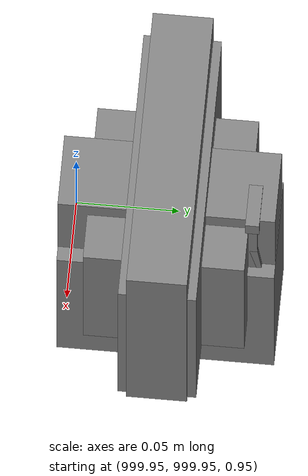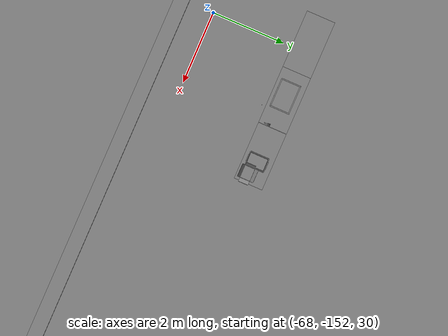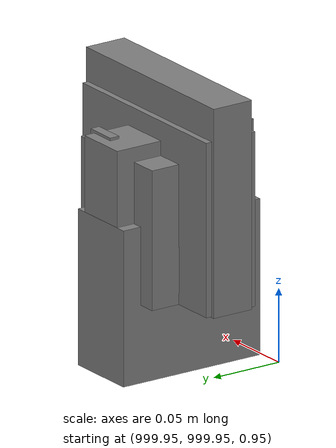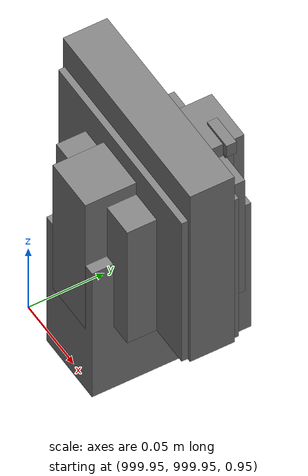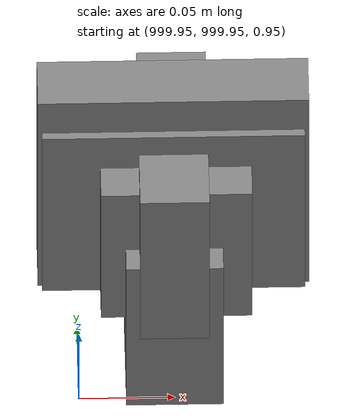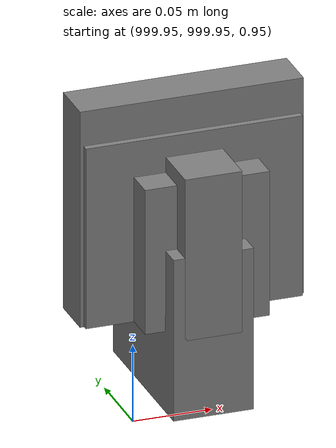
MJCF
<mujoco>
    <option gravity="0.000000000 0.000000000 -9.810000420" timestep="0.0049999999" integrator="implicitfast" density="1.225" viscosity="1.8000001e-05" noslip_iterations="10" iterations="100" sdf_iterations="50">
        <flag multiccd="disable"/>
    </option>
    <size memory="1000M"/>
    <compiler coordinate="local"/>
    <worldbody>
        <light cutoff="30" pos="0 1 1" dir="0 -1 -2"/>
        <light cutoff="30" pos="0 -1 1" dir="0 1 -2"/>
        <body pos="1000.000000000 1000.000000000 1.000000000" euler="0.000000000 0.000000000 180.000000000" name="openloong_gripper_2f85_fix_base_usda_battery_01">
            <geom contype="1" conaffinity="1" density="1000" type="box" material="" rgba="0.500000000 0.500000000 0.500000000 1.000000000" solimp="0.899999976 0.949999988 0.001000000" friction="1.000000000 0.005000000 0.000100000" solref="0.020000000 1.000000000" margin="0" condim="3" group="0" pos="-0.011123657 -0.041940309 0.101691343" quat="1.000000000 0.000000000 0.000000000 0.000000000" size="0.010800000 0.003375000 0.004725000" name="openloong_gripper_2f85_fix_base_usda_geom_13599F14_20D7_49FD_8F06_C7F20E14068A"/>
            <geom contype="1" conaffinity="1" density="1000" type="box" material="" rgba="0.500000000 0.500000000 0.500000000 1.000000000" solimp="0.899999976 0.949999988 0.001000000" friction="1.000000000 0.005000000 0.000100000" solref="0.020000000 1.000000000" margin="0" condim="3" group="0" pos="-0.010876465 -0.044247437 0.047066893" quat="0.998702705 -0.050920475 0.000000000 0.000000000" size="0.009450001 0.002700000 0.024975000" name="openloong_gripper_2f85_fix_base_usda_geom_7DE36F59_6F9D_4959_8D1E_090C5A07AEB7"/>
            <geom contype="1" conaffinity="1" density="1000" type="box" material="" rgba="0.500000000 0.500000000 0.500000000 1.000000000" solimp="0.899999976 0.949999988 0.001000000" friction="1.000000000 0.005000000 0.000100000" solref="0.020000000 1.000000000" margin="0" condim="3" group="0" pos="-0.001235962 -0.000659180 0.047381196" quat="1.000000000 0.000000000 0.000000000 0.000000000" size="0.039420001 0.039150000 0.047250003" name="openloong_gripper_2f85_fix_base_usda_geom_DB029010_837B_4696_B0AA_F5D7F4CDAB3B"/>
            <geom contype="1" conaffinity="1" density="1000" type="box" material="" rgba="0.500000000 0.500000000 0.500000000 1.000000000" solimp="0.899999976 0.949999988 0.001000000" friction="1.000000000 0.005000000 0.000100000" solref="0.020000000 1.000000000" margin="0" condim="3" group="0" pos="-0.010876465 -0.039138794 0.009851727" quat="1.000000000 0.000000000 0.000000000 0.000000000" size="0.009450001 0.010800000 0.013500000" name="openloong_gripper_2f85_fix_base_usda_geom_A862B994_0066_4465_A785_298C45288B93"/>
            <geom contype="1" conaffinity="1" density="1000" type="box" material="" rgba="0.500000000 0.500000000 0.500000000 1.000000000" solimp="0.899999976 0.949999988 0.001000000" friction="1.000000000 0.005000000 0.000100000" solref="0.020000000 1.000000000" margin="0" condim="3" group="0" pos="-0.010876465 -0.041528322 0.071508206" quat="1.000000000 0.000000000 0.000000000 0.000000000" size="0.009450001 0.002700000 0.027000001" name="openloong_gripper_2f85_fix_base_usda_geom_B13A05F1_7EC1_44D6_8F7B_DA0331CA1B5D"/>
            <freejoint name="openloong_gripper_2f85_fix_base_usda_battery_01_joint"/>
            <site size="0.005000000 0.005000000 0.005000000" rgba="0.500000000 0.500000000 0.500000000 1.000000000" pos="0.000000000 0.000000000 0.000000000" quat="0.999961913 0.008726500 0.000000000 0.000000000" group="0" type="sphere" name="openloong_gripper_2f85_fix_base_usda_battery_01site"/>
        </body>
        <body pos="-66.034713745 -149.771591187 31.168996811" euler="-30.905776978 -88.381317139 -11.153171539" mocap="true" name="spotlight3_SpotLight"/>
        <body pos="1000.000000000 1000.000000000 1.000000000" euler="0.000000000 0.000000000 180.000000000" name="openloong_gripper_2f85_fix_base_usda_cpu_fan">
            <geom contype="1" conaffinity="1" density="1000" type="box" material="" rgba="0.500000000 0.500000000 0.500000000 1.000000000" solimp="0.899999976 0.949999988 0.001000000" friction="1.000000000 0.005000000 0.000100000" solref="0.020000000 1.000000000" margin="0" condim="3" group="0" pos="0.000000000 0.000000000 0.070034981" quat="0.000000000 0.000000000 0.000000000 1.000000000" size="0.070700005 0.014699999 0.070700005" name="openloong_gripper_2f85_fix_base_usda_geom_196C9316_5AA1_450A_BDA0_5EECCCB3EC6C"/>
            <freejoint name="openloong_gripper_2f85_fix_base_usda_cpu_fan_joint"/>
            <site size="0.005000000 0.005000000 0.005000000" rgba="0.500000000 0.500000000 0.500000000 1.000000000" pos="0.000000000 0.000000000 0.000000000" quat="0.999961913 0.008726535 0.000000000 0.000000000" group="0" type="sphere" name="openloong_gripper_2f85_fix_base_usda_cpu_fancsite"/>
        </body>
        <body pos="1000.000000000 1000.000000000 1.000000000" euler="0.000000000 0.000000000 180.000000000" name="openloong_gripper_2f85_fix_base_usda_wifi_box">
            <geom contype="1" conaffinity="1" density="1000" type="box" material="" rgba="0.500000000 0.500000000 0.500000000 1.000000000" solimp="0.899999976 0.949999988 0.001000000" friction="1.000000000 0.005000000 0.000100000" solref="0.020000000 1.000000000" margin="0" condim="3" group="0" pos="0.000000000 0.000000000 0.058978677" quat="0.000000000 0.000000047 0.000000000 1.000000000" size="0.068499997 0.018999999 0.059000000" name="openloong_gripper_2f85_fix_base_usda_geom_7DD1AA06_7407_4205_B3C7_09E42B5CC1EA"/>
            <freejoint name="openloong_gripper_2f85_fix_base_usda_wifi_box_joint"/>
            <site size="0.005000000 0.005000000 0.005000000" rgba="0.500000000 0.500000000 0.500000000 1.000000000" pos="0.000000000 0.000000000 0.000000000" quat="0.999961913 0.008726500 0.000000000 0.000000000" group="0" type="sphere" name="openloong_gripper_2f85_fix_base_usda_wifi_boxsite"/>
        </body>
        <body pos="1000.000000000 1000.000000000 1.000000000" euler="0.000011953 0.000005123 -179.999984741" name="openloong_gripper_2f85_fix_base_usda_intel_box">
            <geom contype="1" conaffinity="1" density="1000" type="box" material="" rgba="0.500000000 0.500000000 0.500000000 1.000000000" solimp="0.899999976 0.949999988 0.001000000" friction="1.000000000 0.005000000 0.000100000" solref="0.020000000 1.000000000" margin="0" condim="3" group="0" pos="0.000000000 -0.000067139 0.000082284" quat="0.707106709 0.000000225 0.000000253 0.707106650" size="0.052800003 0.025300000 0.052800003" name="openloong_gripper_2f85_fix_base_usda_geom_61D0788E_A74C_4741_A6C0_EE524847AFF3"/>
            <freejoint name="openloong_gripper_2f85_fix_base_usda_intel_box_joint"/>
            <site size="0.005000000 0.005000000 0.005000000" rgba="0.500000000 0.500000000 0.500000000 1.000000000" pos="0.000000000 0.000000000 0.000000000" quat="0.999961913 0.008726500 0.000000000 0.000000000" group="0" type="sphere" name="openloong_gripper_2f85_fix_base_usda_intel_boxsite"/>
        </body>
        <body pos="-65.954460144 -148.929870605 31.168540955" euler="-90.143600464 -16.233057022 82.584335327" mocap="true" name="spotlight5_SpotLight"/>
        <body pos="1000.000000000 999.999938965 1.000000000" euler="0.000000000 0.000000000 180.000000000" name="openloong_gripper_2f85_fix_base_usda_intelcore_i5">
            <geom contype="1" conaffinity="1" density="1000" type="box" material="" rgba="0.500000000 0.500000000 0.500000000 1.000000000" solimp="0.899999976 0.949999988 0.001000000" friction="1.000000000 0.005000000 0.000100000" solref="0.020000000 1.000000000" margin="0" condim="3" group="0" pos="0.000000000 0.000000000 0.051722717" quat="0.707106709 0.000000000 0.000000000 -0.707106769" size="0.052800000 0.018080002 0.052800000" name="openloong_gripper_2f85_fix_base_usda_geom_B33F262D_11CE_4F58_AFF4_5AFFFDED86EF"/>
            <freejoint name="openloong_gripper_2f85_fix_base_usda_intelcore_i5_joint"/>
            <site size="0.005000000 0.005000000 0.005000000" rgba="0.500000000 0.500000000 0.500000000 1.000000000" pos="0.000000000 0.000000000 0.000000000" quat="0.999961913 0.008726534 0.000000000 0.000000000" group="0" type="sphere" name="openloong_gripper_2f85_fix_base_usda_intelcore_i5site"/>
        </body>
        <body pos="-65.827209473 -148.893142700 31.170110703" euler="18.547897339 28.499071121 168.000869751" mocap="true" name="spotlight2_SpotLight"/>
        <body pos="-64.866622925 -149.383972168 30.183746338" euler="89.999984741 89.999946594 0.000000000" name="openloong_gripper_2f85_fix_base_usda_bluebox_01">
            <geom contype="1" conaffinity="1" density="1000" type="box" material="" rgba="0.500000000 0.500000000 0.500000000 1.000000000" solimp="0.899999976 0.949999988 0.001000000" friction="1.000000000 0.005000000 0.000100000" solref="0.020000000 1.000000000" margin="0" condim="3" group="0" pos="0.276580811 0.187225342 0.000068665" quat="0.707106948 0.000077471 0.707106352 0.000077486" size="0.100000001 0.057999998 0.010000000" name="openloong_gripper_2f85_fix_base_usda_geom_9F1F165E_B7CD_42A1_AA36_FE8F9803342F"/>
            <geom contype="1" conaffinity="1" density="1000" type="box" material="" rgba="0.500000000 0.500000000 0.500000000 1.000000000" solimp="0.899999976 0.949999988 0.001000000" friction="1.000000000 0.005000000 0.000100000" solref="0.020000000 1.000000000" margin="0" condim="3" group="0" pos="0.000000000 0.002883911 0.000000000" quat="0.999999881 0.000000000 0.000000000 0.000000000" size="0.254000008 0.003000000 0.172000006" name="openloong_gripper_2f85_fix_base_usda_geom_BB93D688_854A_4444_A4FA_796D258467BE"/>
            <geom contype="1" conaffinity="1" density="1000" type="box" material="" rgba="0.500000000 0.500000000 0.500000000 1.000000000" solimp="0.899999976 0.949999988 0.001000000" friction="1.000000000 0.005000000 0.000100000" solref="0.020000000 1.000000000" margin="0" condim="3" group="0" pos="0.000000000 0.124874115 0.173484802" quat="0.999796331 0.020176515 -0.000000015 0.000000030" size="0.259999990 0.119999997 0.007000000" name="openloong_gripper_2f85_fix_base_usda_geom_60716A09_1B8F_4ABE_BB71_8C0543BF1598"/>
            <geom contype="1" conaffinity="1" density="1000" type="box" material="" rgba="0.500000000 0.500000000 0.500000000 1.000000000" solimp="0.899999976 0.949999988 0.001000000" friction="1.000000000 0.005000000 0.000100000" solref="0.020000000 1.000000000" margin="0" condim="3" group="0" pos="0.000000000 0.124874115 -0.173469543" quat="0.999796331 -0.020176545 -0.000000015 0.000000000" size="0.259999990 0.119999997 0.007000000" name="openloong_gripper_2f85_fix_base_usda_geom_D57C2BB4_A031_4775_BECE_A5D5FB8C5CD1"/>
            <geom contype="1" conaffinity="1" density="1000" type="box" material="" rgba="0.500000000 0.500000000 0.500000000 1.000000000" solimp="0.899999976 0.949999988 0.001000000" friction="1.000000000 0.005000000 0.000100000" solref="0.020000000 1.000000000" margin="0" condim="3" group="0" pos="0.000000000 0.214008331 0.188980103" quat="0.999912977 0.013176724 0.000000015 0.000000000" size="0.259999990 0.029999999 0.012500000" name="openloong_gripper_2f85_fix_base_usda_geom_679FF5A8_DE63_4148_B8F2_1DC909A9ECB0"/>
            <geom contype="1" conaffinity="1" density="1000" type="box" material="" rgba="0.500000000 0.500000000 0.500000000 1.000000000" solimp="0.899999976 0.949999988 0.001000000" friction="1.000000000 0.005000000 0.000100000" solref="0.020000000 1.000000000" margin="0" condim="3" group="0" pos="-0.258361816 0.125289917 0.001876831" quat="0.702796936 -0.020792112 0.710783124 0.020769298" size="0.189999998 0.119999997 0.009000000" name="openloong_gripper_2f85_fix_base_usda_geom_1AAFBEC1_5359_4E19_A3A9_1731F36FFA16"/>
            <geom contype="1" conaffinity="1" density="1000" type="box" material="" rgba="0.500000000 0.500000000 0.500000000 1.000000000" solimp="0.899999976 0.949999988 0.001000000" friction="1.000000000 0.005000000 0.000100000" solref="0.020000000 1.000000000" margin="0" condim="3" group="0" pos="0.000000000 0.214008331 -0.188980103" quat="0.999912977 -0.013176769 0.000000030 0.000000015" size="0.259999990 0.029999999 0.012500000" name="openloong_gripper_2f85_fix_base_usda_geom_177E0B8A_B14B_4BD0_A138_4E4F3FE077B8"/>
            <geom contype="1" conaffinity="1" density="1000" type="box" material="" rgba="0.500000000 0.500000000 0.500000000 1.000000000" solimp="0.899999976 0.949999988 0.001000000" friction="1.000000000 0.005000000 0.000100000" solref="0.020000000 1.000000000" margin="0" condim="3" group="0" pos="-0.276611328 0.187225342 0.000068665" quat="0.707106650 0.000077441 0.707106709 0.000077456" size="0.100000001 0.057999998 0.010000000" name="openloong_gripper_2f85_fix_base_usda_geom_96FCD75C_B610_46B2_BF2E_4FABB0A27DD3"/>
            <geom contype="1" conaffinity="1" density="1000" type="box" material="" rgba="0.500000000 0.500000000 0.500000000 1.000000000" solimp="0.899999976 0.949999988 0.001000000" friction="1.000000000 0.005000000 0.000100000" solref="0.020000000 1.000000000" margin="0" condim="3" group="0" pos="0.258331299 0.125289917 0.001876831" quat="0.702851415 0.018856421 0.710823774 -0.019329369" size="0.189999998 0.119999997 0.009000000" name="openloong_gripper_2f85_fix_base_usda_geom_7AB022FE_0C8B_41FE_824F_1E75EDB0CBD7"/>
            <freejoint name="openloong_gripper_2f85_fix_base_usda_bluebox_01_joint"/>
            <site size="0.005000000 0.005000000 0.005000000" rgba="0.500000000 0.500000000 0.500000000 1.000000000" pos="0.000000000 0.000000000 0.000000000" quat="0.999961913 0.008726534 0.000000000 0.000000000" group="0" type="sphere" name="openloong_gripper_2f85_fix_base_usda_bluebox_01site"/>
        </body>
        <body pos="-64.496299744 -149.491867065 30.235729218" euler="0.000000000 0.000000000 89.999946594" name="openloong_gripper_2f85_fix_base_usda_cardboardbox_01">
            <geom contype="1" conaffinity="1" density="1000" type="box" material="" rgba="0.500000000 0.500000000 0.500000000 1.000000000" solimp="0.899999976 0.949999988 0.001000000" friction="1.000000000 0.005000000 0.000100000" solref="0.020000000 1.000000000" margin="0" condim="3" group="0" pos="-0.003166199 -0.004086494 0.005052090" quat="1.000000000 0.000000000 0.000000000 0.000000000" size="0.142499998 0.177500010 0.005000000" name="openloong_gripper_2f85_fix_base_usda_geom_1F3A11BD_1855_433B_91B6_AEF545DD9E6F"/>
            <geom contype="1" conaffinity="1" density="1000" type="box" material="" rgba="0.500000000 0.500000000 0.500000000 1.000000000" solimp="0.899999976 0.949999988 0.001000000" friction="1.000000000 0.005000000 0.000100000" solref="0.020000000 1.000000000" margin="0" condim="3" group="0" pos="-0.003166199 0.170316696 0.150570869" quat="1.000000000 0.000000000 0.000000000 0.000000000" size="0.142499998 0.005000000 0.149999991" name="openloong_gripper_2f85_fix_base_usda_geom_5BFBC627_D1A1_4A42_95CD_1BF973F8C3D4"/>
            <geom contype="1" conaffinity="1" density="1000" type="box" material="" rgba="0.500000000 0.500000000 0.500000000 1.000000000" solimp="0.899999976 0.949999988 0.001000000" friction="1.000000000 0.005000000 0.000100000" solref="0.020000000 1.000000000" margin="0" condim="3" group="0" pos="-0.147399902 -0.005307198 0.150570869" quat="1.000000000 0.000000000 0.000000000 0.000000000" size="0.005000000 0.177500010 0.149999991" name="openloong_gripper_2f85_fix_base_usda_geom_2E6D406D_3908_441B_91D2_4E5B8672E8F9"/>
            <geom contype="1" conaffinity="1" density="1000" type="box" material="" rgba="0.500000000 0.500000000 0.500000000 1.000000000" solimp="0.899999976 0.949999988 0.001000000" friction="1.000000000 0.005000000 0.000100000" solref="0.020000000 1.000000000" margin="0" condim="3" group="0" pos="0.140275955 -0.005307198 0.150570869" quat="1.000000000 0.000000000 0.000000000 0.000000000" size="0.005000000 0.177500010 0.149999991" name="openloong_gripper_2f85_fix_base_usda_geom_FA18B469_085A_48D7_AD4B_2C4E156A78BA"/>
            <geom contype="1" conaffinity="1" density="1000" type="box" material="" rgba="0.500000000 0.500000000 0.500000000 1.000000000" solimp="0.899999976 0.949999988 0.001000000" friction="1.000000000 0.005000000 0.000100000" solref="0.020000000 1.000000000" margin="0" condim="3" group="0" pos="-0.003166199 -0.181550980 0.150570869" quat="1.000000000 0.000000000 0.000000000 0.000000000" size="0.142499998 0.005000000 0.149999991" name="openloong_gripper_2f85_fix_base_usda_geom_99B561F9_8860_488E_B40B_56F0DA87B628"/>
            <freejoint name="openloong_gripper_2f85_fix_base_usda_cardboardbox_01_joint"/>
            <site size="0.005000000 0.005000000 0.005000000" rgba="0.500000000 0.500000000 0.500000000 1.000000000" pos="0.000000000 0.000000000 0.000000000" quat="0.999961913 0.008726535 0.000000000 0.000000000" group="0" type="sphere" name="openloong_gripper_2f85_fix_base_usda_site_243B3E28_E543_498E_AB01_48611D92F73E"/>
            <body pos="0.139160156 -0.004048347 0.301930904" euler="-179.999954224 49.383502960 179.999954224" name="openloong_gripper_2f85_fix_base_usda_A1_006">
                <geom contype="1" conaffinity="1" density="1000" type="box" material="" rgba="0.500000000 0.500000000 0.500000000 1.000000000" solimp="0.899999976 0.949999988 0.001000000" friction="1.000000000 0.005000000 0.000100000" solref="0.020000000 1.000000000" margin="0" condim="3" group="0" pos="-0.071587563 0.000009537 0.001745224" quat="0.999999881 0.000000000 0.000000000 0.000000000" size="0.071249999 0.179999992 0.002500000" name="openloong_gripper_2f85_fix_base_usda_geom_90B01449_861E_4752_ADA2_F980C24075E0"/>
                <joint armature="0" stiffness="0.07" damping="0.0099999998" axis="0.000000 1.000000 0.000000" type="hinge" name="openloong_gripper_2f85_fix_base_usda_A1_006"/>
            </body>
            <body pos="-0.145902634 -0.004086494 0.301938057" euler="-180.000000000 -60.000011444 -180.000000000" name="openloong_gripper_2f85_fix_base_usda_A2_006">
                <geom contype="1" conaffinity="1" density="1000" type="box" material="" rgba="0.500000000 0.500000000 0.500000000 1.000000000" solimp="0.899999976 0.949999988 0.001000000" friction="1.000000000 0.005000000 0.000100000" solref="0.020000000 1.000000000" margin="0" condim="3" group="0" pos="0.071268082 0.000009537 0.002717972" quat="0.000002921 0.000000000 -0.000000030 0.999999881" size="0.071249999 0.179999992 0.002500000" name="openloong_gripper_2f85_fix_base_usda_geom_E24C9EBA_73F7_4627_97F9_91E991E37F1F"/>
                <joint armature="0" stiffness="0.07" damping="0.0099999998" axis="0.000000 1.000000 0.000000" type="hinge" name="openloong_gripper_2f85_fix_base_usda_A2_006"/>
            </body>
            <body pos="-0.003385544 0.175991058 0.301930904" euler="-125.858116150 -0.000004561 0.000002331" name="openloong_gripper_2f85_fix_base_usda_B2_006">
                <geom contype="1" conaffinity="1" density="1000" type="box" material="" rgba="0.500000000 0.500000000 0.500000000 1.000000000" solimp="0.899999976 0.949999988 0.001000000" friction="1.000000000 0.005000000 0.000100000" solref="0.020000000 1.000000000" margin="0" condim="3" group="0" pos="0.000009537 -0.070939064 -0.002470016" quat="0.999614120 0.027776197 -0.000000015 0.000000030" size="0.137500003 0.064999998 0.005000000" name="openloong_gripper_2f85_fix_base_usda_geom_40A87867_79EA_43B1_992B_A582987BCF42"/>
                <joint armature="0" stiffness="0.07" damping="0.0099999998" axis="1.000000 0.000000 0.000000" type="hinge" name="openloong_gripper_2f85_fix_base_usda_B2_006"/>
            </body>
            <body pos="-0.003385544 -0.184140205 0.301938057" euler="147.805557251 0.000000000 0.000000000" name="openloong_gripper_2f85_fix_base_usda_B1_006">
                <geom contype="1" conaffinity="1" density="1000" type="box" material="" rgba="0.500000000 0.500000000 0.500000000 1.000000000" solimp="0.899999976 0.949999988 0.001000000" friction="1.000000000 0.005000000 0.000100000" solref="0.020000000 1.000000000" margin="0" condim="3" group="0" pos="-0.000028610 0.070202351 -0.002703667" quat="0.999614179 -0.027776167 0.000000000 0.000000000" size="0.137500003 0.064999998 0.005000000" name="openloong_gripper_2f85_fix_base_usda_geom_03C8229D_405C_4A7C_A7E3_BBD5D12658B7"/>
                <joint armature="0" stiffness="0.07" damping="0.0099999998" axis="1.000000 0.000000 0.000000" type="hinge" name="openloong_gripper_2f85_fix_base_usda_B1_006"/>
            </body>
        </body>
        <body pos="-65.882858276 -149.481979370 30.229999542" euler="-64.487716675 0.000000000 0.000000000" name="openloong_gripper_2f85_fix_base_usda_Barcode">
            <geom contype="1" conaffinity="1" density="1000" type="box" material="" rgba="0.500000000 0.500000000 0.500000000 1.000000000" solimp="0.899999976 0.949999988 0.001000000" friction="1.000000000 0.005000000 0.000100000" solref="0.020000000 1.000000000" margin="0" condim="3" group="0" pos="0.000000000 0.013038635 0.001419067" quat="0.000000000 0.000000000 0.000000000 1.000000119" size="0.034000002 0.010000000 0.017999999" name="openloong_gripper_2f85_fix_base_usda_geom_C1FD140D_2861_4367_8EB5_D6EB4E1FB4DD"/>
            <geom contype="1" conaffinity="1" density="1000" type="box" material="" rgba="0.500000000 0.500000000 0.500000000 1.000000000" solimp="0.899999976 0.949999988 0.001000000" friction="1.000000000 0.005000000 0.000100000" solref="0.020000000 1.000000000" margin="0" condim="3" group="0" pos="0.000000000 -0.035301208 -0.007095337" quat="0.000000000 0.000000000 -0.043619365 0.999048233" size="0.028999999 0.010000000 0.020000000" name="openloong_gripper_2f85_fix_base_usda_geom_BC1400DF_26D5_43B7_A6B6_3AB714BCBBC7"/>
            <geom contype="1" conaffinity="1" density="1000" type="box" material="" rgba="0.500000000 0.500000000 0.500000000 1.000000000" solimp="0.899999976 0.949999988 0.001000000" friction="1.000000000 0.005000000 0.000100000" solref="0.020000000 1.000000000" margin="0" condim="3" group="0" pos="0.000000000 -0.043411255 -0.011749268" quat="0.922262907 0.386563420 0.000000000 0.000000000" size="0.026000001 0.010000000 0.020000000" name="openloong_gripper_2f85_fix_base_usda_geom_38A087F8_CF92_49D9_B2E7_EE27A789D36B"/>
            <geom contype="1" conaffinity="1" density="1000" type="box" material="" rgba="0.500000000 0.500000000 0.500000000 1.000000000" solimp="0.899999976 0.949999988 0.001000000" friction="1.000000000 0.005000000 0.000100000" solref="0.020000000 1.000000000" margin="0" condim="3" group="0" pos="0.000000000 -0.016967773 -0.031860352" quat="0.000000000 0.000000000 0.000000000 1.000000119" size="0.008000000 0.010000000 0.013000000" name="openloong_gripper_2f85_fix_base_usda_geom_6FFE30A6_1663_463F_8229_26E6B2C9EA16"/>
            <geom contype="1" conaffinity="1" density="1000" type="box" material="" rgba="0.500000000 0.500000000 0.500000000 1.000000000" solimp="0.899999976 0.949999988 0.001000000" friction="1.000000000 0.005000000 0.000100000" solref="0.020000000 1.000000000" margin="0" condim="3" group="0" pos="0.000000000 -0.001869202 0.000312805" quat="0.953716993 0.300705761 0.000000000 0.000000000" size="0.032000002 0.010000000 0.018999999" name="openloong_gripper_2f85_fix_base_usda_geom_71371D26_8218_4970_A065_FDCB764AC152"/>
            <geom contype="1" conaffinity="1" density="1000" type="box" material="" rgba="0.500000000 0.500000000 0.500000000 1.000000000" solimp="0.899999976 0.949999988 0.001000000" friction="1.000000000 0.005000000 0.000100000" solref="0.020000000 1.000000000" margin="0" condim="3" group="0" pos="0.000000000 -0.019531250 -0.003173828" quat="0.953716993 0.300705761 0.000000000 0.000000000" size="0.030999999 0.010000000 0.020000000" name="openloong_gripper_2f85_fix_base_usda_geom_8133A392_BA91_4D9B_B9EC_8698976EEA9E"/>
            <geom contype="1" conaffinity="1" density="1000" type="box" material="" rgba="0.500000000 0.500000000 0.500000000 1.000000000" solimp="0.899999976 0.949999988 0.001000000" friction="1.000000000 0.005000000 0.000100000" solref="0.020000000 1.000000000" margin="0" condim="3" group="0" pos="0.000000000 -0.035301208 -0.007095337" quat="0.953716993 0.300705761 0.000000000 0.000000000" size="0.028999999 0.010000000 0.020000000" name="openloong_gripper_2f85_fix_base_usda_geom_A9B66EB9_8694_458C_8B64_A69983BCC027"/>
            <geom contype="1" conaffinity="1" density="1000" type="box" material="" rgba="0.500000000 0.500000000 0.500000000 1.000000000" solimp="0.899999976 0.949999988 0.001000000" friction="1.000000000 0.005000000 0.000100000" solref="0.020000000 1.000000000" margin="0" condim="3" group="0" pos="0.000000000 -0.042617798 -0.071121216" quat="0.000000000 0.000000000 0.000000000 1.000000119" size="0.013000000 0.021000000 0.059999999" name="openloong_gripper_2f85_fix_base_usda_geom_C08547A2_17FF_47CA_B7FD_15B907C31479"/>
            <freejoint name="openloong_gripper_2f85_fix_base_usda_Barcode_joint"/>
            <site size="0.005000000 0.005000000 0.005000000" rgba="0.500000000 0.500000000 0.500000000 1.000000000" pos="0.000000000 0.000000000 0.000000000" quat="1.000000000 0.000000000 0.000000000 0.000000000" group="0" type="sphere" name="openloong_gripper_2f85_fix_base_usda_Barcode_site"/>
        </body>
        <body pos="-66.745018005 -149.392349243 30.184000015" euler="0.000000000 0.000000000 89.999946594" name="[22331186770466]_Basket_01">
            <geom contype="1" conaffinity="1" density="1000" type="box" material="" rgba="0.500000000 0.500000000 0.500000000 1.000000000" solimp="0.899999976 0.949999988 0.001000000" friction="1.000000000 0.005000000 0.000100000" solref="0.020000000 1.000000000" margin="0" condim="3" group="0" pos="-0.052425385 0.389207840 0.089787483" quat="0.707107008 0.000000000 0.000000000 0.707106411" size="0.014249999 0.014249999 0.059999999" name="[22331186770466]_geom_C9E6A3D0_077C_4422_8A4F_160726889B15"/>
            <geom contype="1" conaffinity="1" density="1000" type="box" material="" rgba="0.500000000 0.500000000 0.500000000 1.000000000" solimp="0.899999976 0.949999988 0.001000000" friction="1.000000000 0.005000000 0.000100000" solref="0.020000000 1.000000000" margin="0" condim="3" group="0" pos="0.264015198 -0.133043289 0.089787483" quat="0.707107008 0.000000000 0.000000000 0.707106411" size="0.014249999 0.014249999 0.059999999" name="[22331186770466]_geom_9C4160C1_FF9F_4C22_845E_AA752689E5D3"/>
            <geom contype="1" conaffinity="1" density="1000" type="box" material="" rgba="0.500000000 0.500000000 0.500000000 1.000000000" solimp="0.899999976 0.949999988 0.001000000" friction="1.000000000 0.005000000 0.000100000" solref="0.020000000 1.000000000" margin="0" condim="3" group="0" pos="-0.264015198 -0.265548706 0.089793205" quat="0.707107008 0.000000000 0.000000000 0.707106411" size="0.014249999 0.014249999 0.059999999" name="[22331186770466]_geom_F1FF6C51_1E94_448F_8FEF_A5CEE92A67A7"/>
            <geom contype="1" conaffinity="1" density="1000" type="box" material="" rgba="0.500000000 0.500000000 0.500000000 1.000000000" solimp="0.899999976 0.949999988 0.001000000" friction="1.000000000 0.005000000 0.000100000" solref="0.020000000 1.000000000" margin="0" condim="3" group="0" pos="-0.160263062 -0.389322281 0.089793205" quat="0.707107008 0.000000000 0.000000000 0.707106411" size="0.014249999 0.014249999 0.059999999" name="[22331186770466]_geom_7FB2F168_5E37_4BBB_9112_E8F29B26C67D"/>
            <geom contype="1" conaffinity="1" density="1000" type="box" material="" rgba="0.500000000 0.500000000 0.500000000 1.000000000" solimp="0.899999976 0.949999988 0.001000000" friction="1.000000000 0.005000000 0.000100000" solref="0.020000000 1.000000000" margin="0" condim="3" group="0" pos="0.162265778 -0.389322281 0.089787483" quat="0.707107008 0.000000000 0.000000000 0.707106411" size="0.014249999 0.014249999 0.059999999" name="[22331186770466]_geom_6E114790_24D6_473E_8D0F_BBBE1AA78BDA"/>
            <geom contype="1" conaffinity="1" density="1000" type="box" material="" rgba="0.500000000 0.500000000 0.500000000 1.000000000" solimp="0.899999976 0.949999988 0.001000000" friction="1.000000000 0.005000000 0.000100000" solref="0.020000000 1.000000000" margin="0" condim="3" group="0" pos="0.264015198 0.389207840 0.089787483" quat="0.707107008 0.000000000 0.000000000 0.707106411" size="0.014249999 0.014249999 0.059999999" name="[22331186770466]_geom_4E12156A_188E_48E2_9270_053959A75C4C"/>
            <geom contype="1" conaffinity="1" density="1000" type="box" material="" rgba="0.500000000 0.500000000 0.500000000 1.000000000" solimp="0.899999976 0.949999988 0.001000000" friction="1.000000000 0.005000000 0.000100000" solref="0.020000000 1.000000000" margin="0" condim="3" group="0" pos="-0.264015198 -0.133043289 0.089793205" quat="0.707107008 0.000000000 0.000000000 0.707106411" size="0.014249999 0.014249999 0.059999999" name="[22331186770466]_geom_679DCE9E_F93E_4FF9_8444_B908ADE26C94"/>
            <geom contype="1" conaffinity="1" density="1000" type="box" material="" rgba="0.500000000 0.500000000 0.500000000 1.000000000" solimp="0.899999976 0.949999988 0.001000000" friction="1.000000000 0.005000000 0.000100000" solref="0.020000000 1.000000000" margin="0" condim="3" group="0" pos="-0.264026642 0.269256592 0.089793205" quat="0.707107008 0.000000000 0.000000000 0.707106411" size="0.014249999 0.014249999 0.059999999" name="[22331186770466]_geom_BDE4F849_C982_4176_A00F_0A72CE0B3B1B"/>
            <geom contype="1" conaffinity="1" density="1000" type="box" material="" rgba="0.500000000 0.500000000 0.500000000 1.000000000" solimp="0.899999976 0.949999988 0.001000000" friction="1.000000000 0.005000000 0.000100000" solref="0.020000000 1.000000000" margin="0" condim="3" group="0" pos="0.054462433 0.389207840 0.089787483" quat="0.707107008 0.000000000 0.000000000 0.707106411" size="0.014249999 0.014249999 0.059999999" name="[22331186770466]_geom_270750DA_BC91_4926_AECC_090077E631B2"/>
            <geom contype="1" conaffinity="1" density="1000" type="box" material="" rgba="0.500000000 0.500000000 0.500000000 1.000000000" solimp="0.899999976 0.949999988 0.001000000" friction="1.000000000 0.005000000 0.000100000" solref="0.020000000 1.000000000" margin="0" condim="3" group="0" pos="0.054462433 -0.389322281 0.089787483" quat="0.707107008 0.000000000 0.000000000 0.707106411" size="0.014249999 0.014249999 0.059999999" name="[22331186770466]_geom_C95B35B1_DE8A_48E7_8D56_DC50DCB1F89B"/>
            <geom contype="1" conaffinity="1" density="1000" type="box" material="" rgba="0.500000000 0.500000000 0.500000000 1.000000000" solimp="0.899999976 0.949999988 0.001000000" friction="1.000000000 0.005000000 0.000100000" solref="0.020000000 1.000000000" margin="0" condim="3" group="0" pos="0.264015198 0.269256592 0.089793205" quat="0.707107008 0.000000000 0.000000000 0.707106411" size="0.014249999 0.014249999 0.059999999" name="[22331186770466]_geom_55EEA291_3CE1_45B8_AED8_B315D467962E"/>
            <geom contype="1" conaffinity="1" density="1000" type="box" material="" rgba="0.500000000 0.500000000 0.500000000 1.000000000" solimp="0.899999976 0.949999988 0.001000000" friction="1.000000000 0.005000000 0.000100000" solref="0.020000000 1.000000000" margin="0" condim="3" group="0" pos="0.264015198 -0.389322281 0.089787483" quat="0.707107008 0.000000000 0.000000000 0.707106411" size="0.014249999 0.014249999 0.059999999" name="[22331186770466]_geom_D021BB46_92C4_4FB6_9B78_37252CFEE024"/>
            <geom contype="1" conaffinity="1" density="1000" type="box" material="" rgba="0.500000000 0.500000000 0.500000000 1.000000000" solimp="0.899999976 0.949999988 0.001000000" friction="1.000000000 0.005000000 0.000100000" solref="0.020000000 1.000000000" margin="0" condim="3" group="0" pos="0.000000000 0.000000000 0.015998840" quat="0.707107008 0.000000000 0.000000000 0.707106411" size="0.403499991 0.279000014 0.015750000" name="[22331186770466]_geom_E4E6B329_3A39_471E_B3BB_DA856E50875A"/>
            <geom contype="1" conaffinity="1" density="1000" type="box" material="" rgba="0.500000000 0.500000000 0.500000000 1.000000000" solimp="0.899999976 0.949999988 0.001000000" friction="1.000000000 0.005000000 0.000100000" solref="0.020000000 1.000000000" margin="0" condim="3" group="0" pos="0.000000000 -0.389476776 0.163619041" quat="0.707107008 0.000000000 0.000000000 0.707106411" size="0.015000000 0.277500004 0.015750000" name="[22331186770466]_geom_20117445_6ECB_475C_9DCE_D9BBB405CC88"/>
            <geom contype="1" conaffinity="1" density="1000" type="box" material="" rgba="0.500000000 0.500000000 0.500000000 1.000000000" solimp="0.899999976 0.949999988 0.001000000" friction="1.000000000 0.005000000 0.000100000" solref="0.020000000 1.000000000" margin="0" condim="3" group="0" pos="0.162265778 0.389207840 0.089787483" quat="0.707107008 0.000000000 0.000000000 0.707106411" size="0.014249999 0.014249999 0.059999999" name="[22331186770466]_geom_293C865A_4521_412C_8757_35020D3E876B"/>
            <geom contype="1" conaffinity="1" density="1000" type="box" material="" rgba="0.500000000 0.500000000 0.500000000 1.000000000" solimp="0.899999976 0.949999988 0.001000000" friction="1.000000000 0.005000000 0.000100000" solref="0.020000000 1.000000000" margin="0" condim="3" group="0" pos="0.000000000 0.389471054 0.163619041" quat="0.707107008 0.000000000 0.000000000 0.707106411" size="0.015000000 0.277500004 0.015750000" name="[22331186770466]_geom_E9D96839_88D7_4982_AE6E_2A851337C305"/>
            <geom contype="1" conaffinity="1" density="1000" type="box" material="" rgba="0.500000000 0.500000000 0.500000000 1.000000000" solimp="0.899999976 0.949999988 0.001000000" friction="1.000000000 0.005000000 0.000100000" solref="0.020000000 1.000000000" margin="0" condim="3" group="0" pos="-0.263511658 0.000000000 0.163619041" quat="0.707107008 0.000000000 0.000000000 0.707106411" size="0.403499991 0.015000000 0.015750000" name="[22331186770466]_geom_9CFC2F59_C1B4_424D_8009_3E75B8766AD4"/>
            <geom contype="1" conaffinity="1" density="1000" type="box" material="" rgba="0.500000000 0.500000000 0.500000000 1.000000000" solimp="0.899999976 0.949999988 0.001000000" friction="1.000000000 0.005000000 0.000100000" solref="0.020000000 1.000000000" margin="0" condim="3" group="0" pos="-0.264015198 0.141334534 0.089793205" quat="0.707107008 0.000000000 0.000000000 0.707106411" size="0.014249999 0.014249999 0.059999999" name="[22331186770466]_geom_69614F2C_7F2B_4315_AC06_9F0774315EFB"/>
            <geom contype="1" conaffinity="1" density="1000" type="box" material="" rgba="0.500000000 0.500000000 0.500000000 1.000000000" solimp="0.899999976 0.949999988 0.001000000" friction="1.000000000 0.005000000 0.000100000" solref="0.020000000 1.000000000" margin="0" condim="3" group="0" pos="0.264015198 -0.265548706 0.089787483" quat="0.707107008 0.000000000 0.000000000 0.707106411" size="0.014249999 0.014249999 0.059999999" name="[22331186770466]_geom_A3D3E6DE_1206_4491_B4C0_B3F40AB282E2"/>
            <geom contype="1" conaffinity="1" density="1000" type="box" material="" rgba="0.500000000 0.500000000 0.500000000 1.000000000" solimp="0.899999976 0.949999988 0.001000000" friction="1.000000000 0.005000000 0.000100000" solref="0.020000000 1.000000000" margin="0" condim="3" group="0" pos="-0.160263062 0.389207840 0.089787483" quat="0.707107008 0.000000000 0.000000000 0.707106411" size="0.014249999 0.014249999 0.059999999" name="[22331186770466]_geom_2A699530_2453_4D51_B38E_2A46CEA87C0A"/>
            <geom contype="1" conaffinity="1" density="1000" type="box" material="" rgba="0.500000000 0.500000000 0.500000000 1.000000000" solimp="0.899999976 0.949999988 0.001000000" friction="1.000000000 0.005000000 0.000100000" solref="0.020000000 1.000000000" margin="0" condim="3" group="0" pos="-0.052425385 -0.389322281 0.089787483" quat="0.707107008 0.000000000 0.000000000 0.707106411" size="0.014249999 0.014249999 0.059999999" name="[22331186770466]_geom_7A4FB56C_EE8D_47FD_9E5D_A39F09E5A4D6"/>
            <geom contype="1" conaffinity="1" density="1000" type="box" material="" rgba="0.500000000 0.500000000 0.500000000 1.000000000" solimp="0.899999976 0.949999988 0.001000000" friction="1.000000000 0.005000000 0.000100000" solref="0.020000000 1.000000000" margin="0" condim="3" group="0" pos="-0.264026642 -0.389322281 0.089793205" quat="0.707107008 0.000000000 0.000000000 0.707106411" size="0.014249999 0.014249999 0.059999999" name="[22331186770466]_geom_52036ECC_EC85_48EA_BAFA_252E16E11EDA"/>
            <geom contype="1" conaffinity="1" density="1000" type="box" material="" rgba="0.500000000 0.500000000 0.500000000 1.000000000" solimp="0.899999976 0.949999988 0.001000000" friction="1.000000000 0.005000000 0.000100000" solref="0.020000000 1.000000000" margin="0" condim="3" group="0" pos="0.264015198 0.141334534 0.089787483" quat="0.707107008 0.000000000 0.000000000 0.707106411" size="0.014249999 0.014249999 0.059999999" name="[22331186770466]_geom_330D0661_7B15_47FD_AC88_32327715019C"/>
            <geom contype="1" conaffinity="1" density="1000" type="box" material="" rgba="0.500000000 0.500000000 0.500000000 1.000000000" solimp="0.899999976 0.949999988 0.001000000" friction="1.000000000 0.005000000 0.000100000" solref="0.020000000 1.000000000" margin="0" condim="3" group="0" pos="-0.264015198 0.389207840 0.089793205" quat="0.707107008 0.000000000 0.000000000 0.707106411" size="0.014249999 0.014249999 0.059999999" name="[22331186770466]_geom_A92BF4A1_5E3D_4478_AAC5_DEACF560B8A5"/>
            <geom contype="1" conaffinity="1" density="1000" type="box" material="" rgba="0.500000000 0.500000000 0.500000000 1.000000000" solimp="0.899999976 0.949999988 0.001000000" friction="1.000000000 0.005000000 0.000100000" solref="0.020000000 1.000000000" margin="0" condim="3" group="0" pos="0.264015198 0.004480362 0.089787483" quat="0.707107008 0.000000000 0.000000000 0.707106411" size="0.014249999 0.014249999 0.059999999" name="[22331186770466]_geom_ECC0F1D1_30C6_47A0_A0BF_4ACD2F6BE21C"/>
            <geom contype="1" conaffinity="1" density="1000" type="box" material="" rgba="0.500000000 0.500000000 0.500000000 1.000000000" solimp="0.899999976 0.949999988 0.001000000" friction="1.000000000 0.005000000 0.000100000" solref="0.020000000 1.000000000" margin="0" condim="3" group="0" pos="0.263694763 -0.000011444 0.163619041" quat="0.707107008 0.000000000 0.000000000 0.707106411" size="0.403499991 0.015000000 0.015750000" name="[22331186770466]_geom_301364B4_1B2A_412B_9022_651EBF8BFCED"/>
            <geom contype="1" conaffinity="1" density="1000" type="box" material="" rgba="0.500000000 0.500000000 0.500000000 1.000000000" solimp="0.899999976 0.949999988 0.001000000" friction="1.000000000 0.005000000 0.000100000" solref="0.020000000 1.000000000" margin="0" condim="3" group="0" pos="-0.264015198 0.004480362 0.089793205" quat="0.707107008 0.000000000 0.000000000 0.707106411" size="0.014249999 0.014249999 0.059999999" name="[22331186770466]_geom_414E01AF_B727_4BA6_B429_9B85E7585B75"/>
            <freejoint name="[22331186770466]_joint_FA60518C_8338_4076_8F8C_4508EE430CF1"/>
        </body>
        <body pos="0.000000000 0.000000000 0.000000000" euler="0.000000000 0.000000000 0.000000000" name="Static Objects_Static Objects">
            <geom contype="1" conaffinity="1" density="1000" type="box" material="" rgba="0.500000000 0.500000000 0.500000000 1.000000000" solimp="0.899999976 0.949999988 0.001000000" friction="1.000000000 0.005000000 0.000100000" solref="0.020000000 1.000000000" margin="0" condim="3" group="0" pos="-67.544113159 -149.365814209 29.727830887" quat="0.500000417 0.499999970 0.499999553 0.499999970" size="0.381000012 0.319999993 0.041000001" name="Static Objects_geom_215798F1_B0CE_42D8_8A86_F7F6CF194F9E"/>
            <geom contype="1" conaffinity="1" density="1000" type="box" material="" rgba="0.500000000 0.500000000 0.500000000 1.000000000" solimp="0.899999976 0.949999988 0.001000000" friction="1.000000000 0.005000000 0.000100000" solref="0.020000000 1.000000000" margin="0" condim="3" group="0" pos="-68.239501953 -149.365814209 30.086868286" quat="0.500000417 0.499999970 0.499999553 0.499999970" size="0.370999992 0.039500002 0.745000005" name="Static Objects_geom_C24CCF81_9781_4BBF_95D0_AC02832D9983"/>
            <geom contype="1" conaffinity="1" density="1000" type="box" material="" rgba="0.500000000 0.500000000 0.500000000 1.000000000" solimp="0.899999976 0.949999988 0.001000000" friction="1.000000000 0.005000000 0.000100000" solref="0.020000000 1.000000000" margin="0" condim="3" group="0" pos="-68.239501953 -149.365814209 30.147235870" quat="0.500000417 0.499999970 0.499999553 0.499999970" size="0.400000006 0.022000000 0.800000012" name="Static Objects_geom_E290127C_3688_4A6E_AEE0_B6E0A062D29A"/>
            <geom contype="1" conaffinity="1" density="1000" type="box" material="" rgba="0.500000000 0.500000000 0.500000000 1.000000000" solimp="0.899999976 0.949999988 0.001000000" friction="1.000000000 0.005000000 0.000100000" solref="0.020000000 1.000000000" margin="0" condim="3" group="0" pos="-68.934890747 -149.365814209 29.727830887" quat="0.500000417 0.499999970 0.499999553 0.499999970" size="0.381000012 0.319999993 0.041000001" name="Static Objects_geom_B669136A_99D3_4D02_BB76_E4A1EAC01EFE"/>
            <geom contype="1" conaffinity="1" density="1000" type="box" material="" rgba="0.500000000 0.500000000 0.500000000 1.000000000" solimp="0.899999976 0.949999988 0.001000000" friction="1.000000000 0.005000000 0.000100000" solref="0.020000000 1.000000000" margin="0" condim="3" group="0" pos="-68.239501953 -149.365814209 29.561563492" quat="0.500000417 0.499999970 0.499999553 0.499999970" size="0.020000000 0.022000000 0.660000026" name="Static Objects_geom_0185FEFF_3A4F_49D6_AB8A_626E5AE57759"/>
            <geom contype="1" conaffinity="1" density="1000" type="box" material="" rgba="0.500000000 0.500000000 0.500000000 1.000000000" solimp="0.899999976 0.949999988 0.001000000" friction="1.000000000 0.005000000 0.000100000" solref="0.020000000 1.000000000" margin="0" condim="3" group="0" pos="-65.945671082 -149.365814209 29.727830887" quat="0.500000417 0.499999970 0.499999553 0.499999970" size="0.381000012 0.319999993 0.041000001" name="Static Objects_geom_64751D80_2142_4349_A908_2A14F1BC3BC9"/>
            <geom contype="1" conaffinity="1" density="1000" type="box" material="" rgba="0.500000000 0.500000000 0.500000000 1.000000000" solimp="0.899999976 0.949999988 0.001000000" friction="1.000000000 0.005000000 0.000100000" solref="0.020000000 1.000000000" margin="0" condim="3" group="0" pos="-66.641059875 -149.365814209 30.086868286" quat="0.500000417 0.499999970 0.499999553 0.499999970" size="0.370999992 0.039500002 0.745000005" name="Static Objects_geom_2B371393_422A_45D6_BCF2_018A49DDEDCB"/>
            <geom contype="1" conaffinity="1" density="1000" type="box" material="" rgba="0.500000000 0.500000000 0.500000000 1.000000000" solimp="0.899999976 0.949999988 0.001000000" friction="1.000000000 0.005000000 0.000100000" solref="0.020000000 1.000000000" margin="0" condim="3" group="0" pos="-66.641059875 -149.365814209 30.147235870" quat="0.500000417 0.499999970 0.499999553 0.499999970" size="0.400000006 0.022000000 0.800000012" name="Static Objects_geom_0ACD8AAF_4AB9_4617_B765_12CB1B03AED4"/>
            <geom contype="1" conaffinity="1" density="1000" type="box" material="" rgba="0.500000000 0.500000000 0.500000000 1.000000000" solimp="0.899999976 0.949999988 0.001000000" friction="1.000000000 0.005000000 0.000100000" solref="0.020000000 1.000000000" margin="0" condim="3" group="0" pos="-67.336448669 -149.365814209 29.727830887" quat="0.500000417 0.499999970 0.499999553 0.499999970" size="0.381000012 0.319999993 0.041000001" name="Static Objects_geom_34AF0C1B_1A94_49B1_827B_FB780EE8074E"/>
            <geom contype="1" conaffinity="1" density="1000" type="box" material="" rgba="0.500000000 0.500000000 0.500000000 1.000000000" solimp="0.899999976 0.949999988 0.001000000" friction="1.000000000 0.005000000 0.000100000" solref="0.020000000 1.000000000" margin="0" condim="3" group="0" pos="-66.641059875 -149.365814209 29.561563492" quat="0.500000417 0.499999970 0.499999553 0.499999970" size="0.020000000 0.022000000 0.660000026" name="Static Objects_geom_F3E8D972_91B3_4297_8B17_960CDEA1DC6A"/>
            <geom contype="1" conaffinity="1" density="1000" type="box" material="" rgba="0.500000000 0.500000000 0.500000000 1.000000000" solimp="0.899999976 0.949999988 0.001000000" friction="1.000000000 0.005000000 0.000100000" solref="0.020000000 1.000000000" margin="0" condim="3" group="0" pos="-64.338577271 -149.365814209 29.727830887" quat="0.500000417 0.499999970 0.499999553 0.499999970" size="0.381000012 0.319999993 0.041000001" name="Static Objects_geom_32CDCA70_7586_4100_8009_926F26F7757F"/>
            <geom contype="1" conaffinity="1" density="1000" type="box" material="" rgba="0.500000000 0.500000000 0.500000000 1.000000000" solimp="0.899999976 0.949999988 0.001000000" friction="1.000000000 0.005000000 0.000100000" solref="0.020000000 1.000000000" margin="0" condim="3" group="0" pos="-65.033966064 -149.365814209 30.086868286" quat="0.500000417 0.499999970 0.499999553 0.499999970" size="0.370999992 0.039500002 0.745000005" name="Static Objects_geom_1D0F9F8B_1313_4F8C_8919_08DC7A531929"/>
            <geom contype="1" conaffinity="1" density="1000" type="box" material="" rgba="0.500000000 0.500000000 0.500000000 1.000000000" solimp="0.899999976 0.949999988 0.001000000" friction="1.000000000 0.005000000 0.000100000" solref="0.020000000 1.000000000" margin="0" condim="3" group="0" pos="-65.033966064 -149.365814209 30.147235870" quat="0.500000417 0.499999970 0.499999553 0.499999970" size="0.400000006 0.022000000 0.800000012" name="Static Objects_geom_0D0886C3_561E_436C_ADC4_5FEC605474F9"/>
            <geom contype="1" conaffinity="1" density="1000" type="box" material="" rgba="0.500000000 0.500000000 0.500000000 1.000000000" solimp="0.899999976 0.949999988 0.001000000" friction="1.000000000 0.005000000 0.000100000" solref="0.020000000 1.000000000" margin="0" condim="3" group="0" pos="-65.729354858 -149.365814209 29.727830887" quat="0.500000417 0.499999970 0.499999553 0.499999970" size="0.381000012 0.319999993 0.041000001" name="Static Objects_geom_CDCAD6C2_C9CF_4A69_8184_E281DC0D8278"/>
            <geom contype="1" conaffinity="1" density="1000" type="box" material="" rgba="0.500000000 0.500000000 0.500000000 1.000000000" solimp="0.899999976 0.949999988 0.001000000" friction="1.000000000 0.005000000 0.000100000" solref="0.020000000 1.000000000" margin="0" condim="3" group="0" pos="-65.033966064 -149.365814209 29.561563492" quat="0.500000417 0.499999970 0.499999553 0.499999970" size="0.020000000 0.022000000 0.660000026" name="Static Objects_geom_006E2D0E_CED5_4354_A6F6_6DBC4CFE7D90"/>
            <geom contype="1" conaffinity="1" density="1000" type="box" material="" rgba="0.500000000 0.500000000 0.500000000 1.000000000" solimp="0.899999976 0.949999988 0.001000000" friction="1.000000000 0.005000000 0.000100000" solref="0.020000000 1.000000000" margin="0" condim="3" group="0" pos="-61.754566193 -137.853729248 33.906845093" quat="0.707107067 0.000000000 0.000000000 0.707106471" size="0.759999990 0.759999990 4.500000000" name="Static Objects_geom_C9E74092_7CDB_497C_8849_019F87378E7E"/>
            <geom contype="1" conaffinity="1" density="1000" type="box" material="" rgba="0.500000000 0.500000000 0.500000000 1.000000000" solimp="0.899999976 0.949999988 0.001000000" friction="1.000000000 0.005000000 0.000100000" solref="0.020000000 1.000000000" margin="0" condim="3" group="0" pos="-57.511135101 -144.927108765 31.707921982" quat="1.000000000 0.000000000 0.000000000 0.000000000" size="0.200000003 8.000000000 2.299999952" name="Static Objects_geom_C2EAA878_B9BC_462C_A96C_B8383F187FCC"/>
            <geom contype="1" conaffinity="1" density="1000" type="box" material="" rgba="0.500000000 0.500000000 0.500000000 1.000000000" solimp="0.899999976 0.949999988 0.001000000" friction="1.000000000 0.005000000 0.000100000" solref="0.020000000 1.000000000" margin="0" condim="3" group="0" pos="-80.517646790 -157.574050903 31.688196182" quat="0.707107067 0.000000000 0.000000000 0.707106471" size="0.600000024 0.600000024 2.299999952" name="Static Objects_geom_4D398764_13E4_45CE_9F2C_38C7BB2ED2F5"/>
            <geom contype="1" conaffinity="1" density="1000" type="box" material="" rgba="0.500000000 0.500000000 0.500000000 1.000000000" solimp="0.899999976 0.949999988 0.001000000" friction="1.000000000 0.005000000 0.000100000" solref="0.020000000 1.000000000" margin="0" condim="3" group="0" pos="-80.711044312 -147.414932251 31.666158676" quat="1.000000000 0.000000000 0.000000000 0.000000000" size="0.200000003 10.000000000 2.299999952" name="Static Objects_geom_BE62BA56_A335_4B75_835C_52F0ACD249B3"/>
            <geom contype="1" conaffinity="1" density="1000" type="box" material="" rgba="0.500000000 0.500000000 0.500000000 1.000000000" solimp="0.899999976 0.949999988 0.001000000" friction="1.000000000 0.005000000 0.000100000" solref="0.020000000 1.000000000" margin="0" condim="3" group="0" pos="-57.687217712 -137.434692383 31.688196182" quat="0.707107067 0.000000000 0.000000000 0.707106471" size="0.600000024 0.600000024 2.299999952" name="Static Objects_geom_01AF5B1D_6554_4114_9731_1A620BC7F285"/>
            <geom contype="1" conaffinity="1" density="1000" type="box" material="" rgba="0.500000000 0.500000000 0.500000000 1.000000000" solimp="0.899999976 0.949999988 0.001000000" friction="1.000000000 0.005000000 0.000100000" solref="0.020000000 1.000000000" margin="0" condim="3" group="0" pos="-69.537033081 -140.263229370 31.714921951" quat="0.707107067 0.000000000 0.000000000 0.707106471" size="0.759999990 4.500000000 2.299999952" name="Static Objects_geom_0BDFC53C_80F8_466D_90DD_A74839E23DF7"/>
            <geom contype="1" conaffinity="1" density="1000" type="box" material="" rgba="0.500000000 0.500000000 0.500000000 1.000000000" solimp="0.899999976 0.949999988 0.001000000" friction="1.000000000 0.005000000 0.000100000" solref="0.020000000 1.000000000" margin="0" condim="3" group="0" pos="-80.073638916 -137.853713989 33.906845093" quat="0.707107067 0.000000000 0.000000000 0.707106471" size="0.759999990 0.759999990 4.500000000" name="Static Objects_geom_99DD41FE_7F8B_4149_B4AC_687B91EF49F5"/>
            <geom contype="1" conaffinity="1" density="1000" type="box" material="" rgba="0.500000000 0.500000000 0.500000000 1.000000000" solimp="0.899999976 0.949999988 0.001000000" friction="1.000000000 0.005000000 0.000100000" solref="0.020000000 1.000000000" margin="0" condim="3" group="0" pos="-73.406707764 -155.734664917 31.707921982" quat="1.000000000 0.000000000 0.000000000 0.000000000" size="0.200000003 3.000000000 2.299999952" name="Static Objects_geom_DB80FF70_0C4B_4690_AC15_5224AC4BC0F5"/>
            <geom contype="1" conaffinity="1" density="1000" type="box" material="" rgba="0.500000000 0.500000000 0.500000000 1.000000000" solimp="0.899999976 0.949999988 0.001000000" friction="1.000000000 0.005000000 0.000100000" solref="0.020000000 1.000000000" margin="0" condim="3" group="0" pos="-68.497543335 -137.448257446 31.707921982" quat="0.707107067 0.000000000 0.000000000 0.707106471" size="0.200000003 14.000000000 2.299999952" name="Static Objects_geom_4ECF717B_9E17_43A5_8D5C_079F31600CB7"/>
            <geom contype="1" conaffinity="1" density="1000" type="cylinder" material="" rgba="0.500000000 0.500000000 0.500000000 1.000000000" solimp="0.899999976 0.949999988 0.001000000" friction="1.000000000 0.005000000 0.000100000" solref="0.020000000 1.000000000" margin="0" condim="3" group="0" pos="-68.868522644 -142.134506226 31.711090088" quat="0.707107067 0.000000000 0.000000000 0.707106471" size="0.509999990 2.299999952 1.000000000" name="Static Objects_geom_F235BBA9_5EA6_4525_B334_FC1CA5204DDA"/>
            <geom contype="1" conaffinity="1" density="1000" type="plane" material="" rgba="0.500000000 0.500000000 0.500000000 1.000000000" solimp="0.899999976 0.949999988 0.001000000" friction="1.000000000 0.005000000 0.000100000" solref="0.020000000 1.000000000" margin="0" condim="3" group="0" pos="-72.873703003 -147.131927490 29.409669876" quat="1.000000000 0.000000000 0.000000000 0.000000000" size="18.000000000 14.000000000 1.000000000" name="Static Objects_geom_E58E414D_E395_42DC_829A_EC5DD2074023"/>
            <geom contype="1" conaffinity="1" density="1000" type="box" material="" rgba="0.500000000 0.500000000 0.500000000 1.000000000" solimp="0.899999976 0.949999988 0.001000000" friction="1.000000000 0.005000000 0.000100000" solref="0.020000000 1.000000000" margin="0" condim="3" group="0" pos="-79.943580627 -157.782272339 31.707921982" quat="0.707107067 0.000000000 0.000000000 0.707106471" size="0.200000003 7.000000000 2.299999952" name="Static Objects_geom_9026D623_01EC_4937_8B79_E55866C0FDE7"/>
            <geom contype="1" conaffinity="1" density="1000" type="box" material="" rgba="0.500000000 0.500000000 0.500000000 1.000000000" solimp="0.899999976 0.949999988 0.001000000" friction="1.000000000 0.005000000 0.000100000" solref="0.020000000 1.000000000" margin="0" condim="3" group="0" pos="-65.421028137 -152.903442383 31.707921982" quat="0.707107067 0.000000000 0.000000000 0.707106471" size="0.200000003 7.800000191 2.299999952" name="Static Objects_geom_9F78A4B5_139D_4EB0_8520_19B867BB0756"/>
            <geom contype="1" conaffinity="1" density="1000" type="box" material="" rgba="0.500000000 0.500000000 0.500000000 1.000000000" solimp="0.899999976 0.949999988 0.001000000" friction="1.000000000 0.005000000 0.000100000" solref="0.020000000 1.000000000" margin="0" condim="3" group="0" pos="-74.776908875 -149.964416504 31.688196182" quat="1.000000000 0.000000000 0.000000000 0.000000000" size="0.600000024 0.409999996 2.299999952" name="Static Objects_geom_6FAC75A0_277E_4BBC_9214_428AA3FD8A1C"/>
            <geom contype="1" conaffinity="1" density="1000" type="cylinder" material="" rgba="0.500000000 0.500000000 0.500000000 1.000000000" solimp="0.899999976 0.949999988 0.001000000" friction="1.000000000 0.005000000 0.000100000" solref="0.020000000 1.000000000" margin="0" condim="3" group="0" pos="-60.161884308 -142.134506226 31.711090088" quat="0.707107067 0.000000000 0.000000000 0.707106471" size="0.509999990 2.299999952 1.000000000" name="Static Objects_geom_FAB56C7B_2B3D_4A76_BD7C_6B8E30C3265E"/>
            <geom contype="1" conaffinity="1" density="1000" type="cylinder" material="" rgba="0.500000000 0.500000000 0.500000000 1.000000000" solimp="0.899999976 0.949999988 0.001000000" friction="1.000000000 0.005000000 0.000100000" solref="0.020000000 1.000000000" margin="0" condim="3" group="0" pos="-75.382453918 -149.963455200 31.711090088" quat="0.707107067 0.000000000 0.000000000 0.707106471" size="0.409999996 2.299999952 1.000000000" name="Static Objects_geom_B31299F9_8FA6_4FBC_9BF2_A0F9833D61C9"/>
            <geom contype="1" conaffinity="1" density="1000" type="cylinder" material="" rgba="0.500000000 0.500000000 0.500000000 1.000000000" solimp="0.899999976 0.949999988 0.001000000" friction="1.000000000 0.005000000 0.000100000" solref="0.020000000 1.000000000" margin="0" condim="3" group="0" pos="-74.154960632 -149.963455200 31.711090088" quat="0.707107067 0.000000000 0.000000000 0.707106471" size="0.409999996 2.299999952 1.000000000" name="Static Objects_geom_8ECB4ABF_AC46_40C1_AC71_7E1FB2C8C65B"/>
            <geom contype="1" conaffinity="1" density="1000" type="cylinder" material="" rgba="0.500000000 0.500000000 0.500000000 1.000000000" solimp="0.899999976 0.949999988 0.001000000" friction="1.000000000 0.005000000 0.000100000" solref="0.020000000 1.000000000" margin="0" condim="3" group="0" pos="-77.566612244 -142.134506226 31.711090088" quat="0.707107067 0.000000000 0.000000000 0.707106471" size="0.509999990 2.299999952 1.000000000" name="Static Objects_geom_4F8EFEF7_5100_4B98_B62D_F45F7811506B"/>
        </body>
        <body pos="-66.291030884 -149.869689941 29.018842697" euler="0.000000000 0.000000000 89.999946594" mocap="true" name="openloong_gripper_2f85_fix_base_usda_leftHandMocap"/>
        <body pos="-66.291030884 -149.869689941 29.018842697" euler="0.000000000 0.000000000 89.999946594" mocap="true" name="openloong_gripper_2f85_fix_base_usda_rightHandMocap"/>
        <body pos="-66.291030884 -149.869689941 30.218843460" euler="0.000000000 0.000000000 89.999946594" name="openloong_gripper_2f85_fix_base_usda_base_link">
            <geom contype="1" conaffinity="1" density="1000" type="mesh" material="" rgba="0.783999979 0.783999979 0.783999979 1.000000000" solimp="0.899999976 0.949999988 0.001000000" friction="1.000000000 0.005000000 0.000100000" solref="0.020000000 1.000000000" margin="0" condim="3" group="3" mesh="base_link" pos="0.000000000 0.000000000 0.000000000" quat="1.000000000 0.000000000 0.000000000 0.000000000" size="1.000000000 1.000000000 1.000000000" name="openloong_gripper_2f85_fix_base_usda__geom_7_27AC45FF_E681_4F6F_BA16_3712A352006B"/>
            <site size="0.005000000 0.005000000 0.005000000" rgba="0.500000000 0.500000000 0.500000000 1.000000000" pos="0.000000000 0.000000000 0.000000000" quat="1.000000000 0.000000000 0.000000000 0.000000000" group="0" type="sphere" name="openloong_gripper_2f85_fix_base_usda_imu"/>
            <inertial mass="22.447001" pos="-0.005664100 -0.001336700 0.238289997" diaginertia="0.374352545 0.277180195 0.220617250" quat="0.999247074 0.035235517 -0.015086859 0.006023135"/>
            <body pos="0.000000000 0.000000000 0.299997330" euler="0.000000000 0.000000000 0.000000000" name="openloong_gripper_2f85_fix_base_usda_dummy_body">
                <geom contype="1" conaffinity="1" density="1000" type="sphere" material="" rgba="0.783999979 0.783999979 0.783999979 1.000000000" solimp="0.899999976 0.949999988 0.001000000" friction="1.000000000 0.005000000 0.000100000" solref="0.020000000 1.000000000" margin="0" condim="3" group="3" pos="0.000000000 0.000000000 0.000000000" quat="1.000000000 0.000000000 0.000000000 0.000000000" size="0.010000000 0.000000000 0.000000000" name="openloong_gripper_2f85_fix_base_usda__geom_8_4514F05D_E276_4E39_A09A_FB3F0AE10D20"/>
                <joint armature="0.0099999998" stiffness="0" damping="0.1" axis="0.000000 0.000000 1.000000" type="hinge" name="openloong_gripper_2f85_fix_base_usda_dummy_joint"/>
                <site size="0.010000000 0.005000000 0.005000000" rgba="0.500000000 0.500000000 0.500000000 1.000000000" pos="0.000000000 0.000000000 0.000000000" quat="1.000000000 0.000000000 0.000000000 0.000000000" group="3" type="sphere" name="openloong_gripper_2f85_fix_base_usda_dummy_site"/>
            </body>
            <body pos="0.009002686 0.000000000 0.406400681" euler="0.000000000 0.000000000 0.000000000" name="openloong_gripper_2f85_fix_base_usda_Link_head_yaw">
                <geom contype="1" conaffinity="1" density="1000" type="mesh" material="" rgba="0.783999979 0.783999979 0.783999979 1.000000000" solimp="0.899999976 0.949999988 0.001000000" friction="1.000000000 0.005000000 0.000100000" solref="0.020000000 1.000000000" margin="0" condim="3" group="3" mesh="Link_head_yaw" pos="0.000000000 0.000000000 0.000000000" quat="1.000000000 0.000000000 0.000000000 0.000000000" size="1.000000000 1.000000000 1.000000000" name="openloong_gripper_2f85_fix_base_usda__geom_10_FE4CA4AD_3E98_4354_A9AE_CA718462FE69"/>
                <inertial mass="0.84249002" pos="0.000000000 -0.002081400 0.044801001" diaginertia="0.000700588 0.000629000 0.000553812" quat="0.706933022 -0.015675601 0.015677100 0.706933022"/>
                <body pos="0.000000000 -0.034599304 0.048500061" euler="0.000000000 0.000000000 0.000000000" name="openloong_gripper_2f85_fix_base_usda_Link_head_pitch">
                    <geom contype="1" conaffinity="1" density="1000" type="mesh" material="" rgba="0.783999979 0.783999979 0.783999979 1.000000000" solimp="0.899999976 0.949999988 0.001000000" friction="1.000000000 0.005000000 0.000100000" solref="0.020000000 1.000000000" margin="0" condim="3" group="3" mesh="Link_head_pitch" pos="0.000000000 0.000000000 0.000000000" quat="1.000000000 0.000000000 0.000000000 0.000000000" size="1.000000000 1.000000000 1.000000000" name="openloong_gripper_2f85_fix_base_usda__geom_12_9F6D5D70_E2B9_4F71_B14E_117D9CC8A312"/>
                    <inertial mass="1.3943" pos="0.020569000 0.033004001 0.125000000" diaginertia="0.006381400 0.006289940 0.004481460" quat="0.973390222 0.008406822 0.228157058 0.019624906"/>
                    <body pos="0.000000000 0.029998779 0.000000000" euler="0.000000000 0.000000000 0.000000000" name="openloong_gripper_2f85_fix_base_usda_neck_center_body">
                        <site size="0.010000000 0.005000000 0.005000000" rgba="0.500000000 0.500000000 0.500000000 1.000000000" pos="0.000000000 0.000000000 0.000000000" quat="1.000000000 0.000000000 0.000000000 0.000000000" group="3" type="sphere" name="openloong_gripper_2f85_fix_base_usda_neck_center_site"/>
                        <body pos="0.020004272 0.000000000 0.149999619" euler="-0.000002229 39.998176575 -90.000205994" name="openloong_gripper_2f85_fix_base_usda_camera_head">
                            <site size="0.010000000 0.005000000 0.005000000" rgba="0.500000000 0.500000000 0.500000000 1.000000000" pos="0.000000000 0.000000000 0.000000000" quat="1.000000000 0.000000000 0.000000000 0.000000000" group="3" type="sphere" name="openloong_gripper_2f85_fix_base_usda_camera_head_site"/>
                        </body>
                    </body>
                </body>
            </body>
            <body pos="0.003997803 -0.161598206 0.392200470" euler="0.000000000 0.000000000 0.000000000" name="openloong_gripper_2f85_fix_base_usda_Link_arm_r_01">
                <geom contype="1" conaffinity="1" density="1000" type="mesh" material="" rgba="0.783999979 0.783999979 0.783999979 1.000000000" solimp="0.899999976 0.949999988 0.001000000" friction="1.000000000 0.005000000 0.000100000" solref="0.020000000 1.000000000" margin="0" condim="3" group="3" mesh="Link_arm_r_01" pos="0.000000000 0.000000000 0.000000000" quat="1.000000000 0.000000000 0.000000000 0.000000000" size="1.000000000 1.000000000 1.000000000" name="openloong_gripper_2f85_fix_base_usda__geom_14_0CD929F3_51F7_4C53_B8FB_4712DD1C2EC2"/>
                <joint armature="0.0099999998" stiffness="0" damping="1" axis="0.000000 -1.000000 0.000000" limited="true" range="-170.000015259 170.000015259" type="hinge" name="openloong_gripper_2f85_fix_base_usda_J_arm_r_01"/>
                <inertial mass="0.75641" pos="0.004494600 -0.038293999 -0.000001874" diaginertia="0.000842990 0.000803050 0.000587120" quat="-0.000163502 0.707098067 0.000812463 0.707115054"/>
                <body pos="-0.041992188 -0.041000366 0.000000000" euler="0.000000000 0.000000000 0.000000000" name="openloong_gripper_2f85_fix_base_usda_Link_arm_r_02">
                    <geom contype="1" conaffinity="1" density="1000" type="mesh" material="" rgba="0.783999979 0.783999979 0.783999979 1.000000000" solimp="0.899999976 0.949999988 0.001000000" friction="1.000000000 0.005000000 0.000100000" solref="0.020000000 1.000000000" margin="0" condim="3" group="3" mesh="Link_arm_r_02" pos="0.000000000 0.000000000 0.000000000" quat="1.000000000 0.000000000 0.000000000 0.000000000" size="1.000000000 1.000000000 1.000000000" name="openloong_gripper_2f85_fix_base_usda__geom_16_A6D7D0EE_9E78_40AB_AAB6_70810D5E255B"/>
                    <joint armature="0.0099999998" stiffness="0" damping="1" axis="-1.000000 0.000000 0.000000" limited="true" range="-105.000244141 105.000244141" type="hinge" name="openloong_gripper_2f85_fix_base_usda_J_arm_r_02"/>
                    <inertial mass="0.98500001" pos="0.041999999 -0.067430697 0.000000000" diaginertia="0.002262690 0.001730990 0.001154020" quat="0.500000000 0.500000000 -0.500000000 0.500000000"/>
                    <body pos="0.041992188 -0.122596741 0.000000000" euler="0.000000000 0.000000000 0.000000000" name="openloong_gripper_2f85_fix_base_usda_Link_arm_r_03">
                        <geom contype="1" conaffinity="1" density="1000" type="mesh" material="" rgba="0.783999979 0.783999979 0.783999979 1.000000000" solimp="0.899999976 0.949999988 0.001000000" friction="1.000000000 0.005000000 0.000100000" solref="0.020000000 1.000000000" margin="0" condim="3" group="3" mesh="Link_arm_r_03" pos="0.000000000 0.000000000 0.000000000" quat="1.000000000 0.000000000 0.000000000 0.000000000" size="1.000000000 1.000000000 1.000000000" name="openloong_gripper_2f85_fix_base_usda__geom_18_B9131A74_6420_48C5_BF86_505D5D22190D"/>
                        <joint armature="0.0099999998" stiffness="0" damping="1" axis="0.000000 -1.000000 0.000000" limited="true" range="-170.000015259 170.000015259" type="hinge" name="openloong_gripper_2f85_fix_base_usda_J_arm_r_03"/>
                        <inertial mass="0.95899999" pos="-0.001413580 -0.164663002 0.020757901" diaginertia="0.002101340 0.002064590 0.000754802" quat="0.560480952 0.454391927 -0.443732947 0.531497955"/>
                        <body pos="0.035293579 -0.177406311 0.023998260" euler="0.000000000 0.000000000 0.000000000" name="openloong_gripper_2f85_fix_base_usda_Link_arm_r_04">
                            <geom contype="1" conaffinity="1" density="1000" type="mesh" material="" rgba="0.783999979 0.783999979 0.783999979 1.000000000" solimp="0.899999976 0.949999988 0.001000000" friction="1.000000000 0.005000000 0.000100000" solref="0.020000000 1.000000000" margin="0" condim="3" group="3" mesh="Link_arm_r_04" pos="0.000000000 0.000000000 0.000000000" quat="1.000000000 0.000000000 0.000000000 0.000000000" size="1.000000000 1.000000000 1.000000000" name="openloong_gripper_2f85_fix_base_usda__geom_20_2E1B06A4_D8D9_44F1_89F1_1E8F20E8982D"/>
                            <joint armature="0.0099999998" stiffness="0" damping="1" axis="-1.000000 0.000000 0.000000" limited="true" range="0.000000000 170.000015259" type="hinge" name="openloong_gripper_2f85_fix_base_usda_J_arm_r_04"/>
                            <inertial mass="0.60000002" pos="-0.038727000 -0.060766999 -0.021003000" diaginertia="0.001092610 0.000712422 0.000645102" quat="0.327701002 0.632602990 -0.467366993 0.523443997"/>
                            <body pos="-0.035293579 -0.103492737 -0.023998260" euler="0.000000000 0.000000000 0.000000000" name="openloong_gripper_2f85_fix_base_usda_Link_arm_r_05">
                                <geom contype="1" conaffinity="1" density="1000" type="mesh" material="" rgba="0.783999979 0.783999979 0.783999979 1.000000000" solimp="0.899999976 0.949999988 0.001000000" friction="1.000000000 0.005000000 0.000100000" solref="0.020000000 1.000000000" margin="0" condim="3" group="3" mesh="Link_arm_r_05" pos="0.000000000 0.000000000 0.000000000" quat="1.000000000 0.000000000 0.000000000 0.000000000" size="1.000000000 1.000000000 1.000000000" name="openloong_gripper_2f85_fix_base_usda__geom_22_3E318E1A_DDAF_4F0E_9873_7BF5A6574E3A"/>
                                <joint armature="0.0099999998" stiffness="0" damping="1" axis="0.000000 -1.000000 0.000000" limited="true" range="-170.000015259 170.000015259" type="hinge" name="openloong_gripper_2f85_fix_base_usda_J_arm_r_05"/>
                                <inertial mass="0.68976003" pos="0.000032712 -0.068658002 -0.000111780" diaginertia="0.002522510 0.002411100 0.000448695" quat="0.707660973 0.706543028 -0.002603360 0.002470550"/>
                                <body pos="-0.026489258 -0.196502686 0.000000000" euler="0.000000000 0.000000000 0.000000000" name="openloong_gripper_2f85_fix_base_usda_Link_arm_r_06">
                                    <geom contype="1" conaffinity="1" density="1000" type="mesh" material="" rgba="0.783999979 0.783999979 0.783999979 1.000000000" solimp="0.899999976 0.949999988 0.001000000" friction="1.000000000 0.005000000 0.000100000" solref="0.020000000 1.000000000" margin="0" condim="3" group="3" mesh="Link_arm_r_06" pos="0.000000000 0.000000000 0.000000000" quat="1.000000000 0.000000000 0.000000000 0.000000000" size="1.000000000 1.000000000 1.000000000" name="openloong_gripper_2f85_fix_base_usda__geom_24_E4765AAB_CFB8_4598_A4A4_96F68F1B8A1E"/>
                                    <joint armature="0.0099999998" stiffness="0" damping="1" axis="1.000000 0.000000 0.000000" limited="true" range="-105.000244141 105.000244141" type="hinge" name="openloong_gripper_2f85_fix_base_usda_J_arm_r_06"/>
                                    <inertial mass="0.28" pos="0.026078001 -0.000000896 0.001663700" diaginertia="0.000156930 0.000145601 0.000104979" quat="0.707080841 0.001851080 0.001883810 0.707127810"/>
                                    <body pos="0.026489258 0.000000000 0.031799316" euler="0.000000000 0.000000000 0.000000000" name="openloong_gripper_2f85_fix_base_usda_Link_arm_r_07">
                                        <geom contype="1" conaffinity="1" density="1000" type="mesh" material="" rgba="0.783999979 0.783999979 0.783999979 1.000000000" solimp="0.899999976 0.949999988 0.001000000" friction="1.000000000 0.005000000 0.000100000" solref="0.020000000 1.000000000" margin="0" condim="3" group="3" mesh="Link_arm_r_07" pos="0.000000000 0.000000000 0.000000000" quat="1.000000000 0.000000000 0.000000000 0.000000000" size="1.000000000 1.000000000 1.000000000" name="openloong_gripper_2f85_fix_base_usda__geom_26_70FB7315_2E21_419E_AAAA_54F8A277CAEA"/>
                                        <joint armature="0.0099999998" stiffness="0" damping="1" axis="0.000000 0.000000 1.000000" limited="true" range="-60.000133514 60.000133514" type="hinge" name="openloong_gripper_2f85_fix_base_usda_J_arm_r_07"/>
                                        <inertial mass="0.61353999" pos="-0.007859000 -0.158170000 -0.027736001" diaginertia="0.003037610 0.002570910 0.000729379" quat="0.427542925 0.443532884 -0.553093910 0.560867906"/>
                                        <body pos="0.000000000 0.286994934 -0.270000458" euler="150.000350952 -0.000001649 -0.000000442" name="openloong_gripper_2f85_fix_base_usda_camera_wrist_r">
                                            <site size="0.010000000 0.005000000 0.005000000" rgba="0.500000000 0.500000000 0.500000000 1.000000000" pos="0.000000000 0.000000000 0.000000000" quat="1.000000000 0.000000000 0.000000000 0.000000000" group="3" type="sphere" name="openloong_gripper_2f85_fix_base_usda_camera_wrist_r_site"/>
                                        </body>
                                        <body pos="0.000000000 -0.220008850 -0.033002853" euler="0.000000000 0.000000000 179.999969482" name="openloong_gripper_2f85_fix_base_usda_ee_center_body_r">
                                            <site size="0.010000000 0.005000000 0.005000000" rgba="0.500000000 0.500000000 0.500000000 1.000000000" pos="0.000000000 0.000000000 0.000000000" quat="1.000000000 0.000000000 0.000000000 0.000000000" group="3" type="sphere" name="openloong_gripper_2f85_fix_base_usda_ee_center_site_r"/>
                                        </body>
                                        <body pos="0.000000000 -0.066001892 -0.031000137" euler="89.999984741 0.000000000 180.000000000" name="openloong_gripper_2f85_fix_base_usda_zbr_base_link">
                                            <geom contype="1" conaffinity="1" density="1000" type="mesh" material="" rgba="0.783999979 0.783999979 0.783999979 1.000000000" solimp="0.899999976 0.949999988 0.001000000" friction="1.000000000 0.005000000 0.000100000" solref="0.020000000 1.000000000" margin="0" condim="3" group="3" mesh="base" pos="0.000000000 0.000003815 -0.000007629" quat="1.000000000 0.000000000 0.000000000 0.000000000" size="1.000000238 1.000000238 1.000000238" name="openloong_gripper_2f85_fix_base_usda__geom_30_2770402E_4CAA_4725_89E6_1EE1B2104BDE"/>
                                            <inertial mass="0.77744102" pos="0.000000000 -0.000027039 0.035467502" diaginertia="0.000260285 0.000225381 0.000152708" quat="0.999998808 -0.001528488 0.000000000 0.000000000"/>
                                            <body pos="-0.030609138 0.004745484 0.065696731" euler="-89.999984741 -0.000000000 0.000000000" name="openloong_gripper_2f85_fix_base_usda_r_left_driver">
                                                <geom contype="1" conaffinity="1" density="1000" type="mesh" material="" rgba="0.783999979 0.783999979 0.783999979 1.000000000" solimp="0.899999976 0.949999988 0.001000000" friction="1.000000000 0.005000000 0.000100000" solref="0.020000000 1.000000000" margin="0" condim="3" group="3" mesh="driver" pos="0.030609138 0.054901138 -0.004699708" quat="0.707106829 0.707106709 0.000000000 -0.000000000" size="1.000000238 1.000000238 1.000000238" name="openloong_gripper_2f85_fix_base_usda__geom_32_A71054AD_D78F_429F_9117_91E0EFAC0AC6"/>
                                                <joint armature="0.0049999999" stiffness="0" damping="0.1" axis="0.000000 0.000000 1.000000" limited="true" range="0.000000000 51.566200256" type="hinge" name="openloong_gripper_2f85_fix_base_usda_r_left_driver_joint"/>
                                                <inertial mass="0.0089956298" pos="0.000000000 0.017754700 0.001073140" diaginertia="0.000001724 0.000001609 0.000000322" quat="0.681301236 0.732003212 0.000000000 0.000000000"/>
                                                <body pos="-0.031402595 0.004524232 -0.010200503" euler="0.000000000 0.000000000 180.000000000" name="openloong_gripper_2f85_fix_base_usda_r_left_coupler">
                                                    <geom contype="1" conaffinity="1" density="1000" type="mesh" material="" rgba="0.783999979 0.783999979 0.783999979 1.000000000" solimp="0.899999976 0.949999988 0.001000000" friction="1.000000000 0.005000000 0.000100000" solref="0.020000000 1.000000000" margin="0" condim="3" group="3" mesh="coupler" pos="-0.062011734 -0.050354015 0.005500795" quat="0.707106829 -0.707106709 0.000000000 -0.000000000" size="1.000000238 1.000000238 1.000000238" name="openloong_gripper_2f85_fix_base_usda__geom_34_A4324925_F6DD_4DAF_8F4C_08900E8F84BF"/>
                                                    <inertial mass="0.0140974" pos="0.000000000 0.003012090 0.023217499" diaginertia="0.000004162 0.000003522 0.000000888" quat="0.705635548 -0.045590367 0.045590367 0.705635548"/>
                                                </body>
                                            </body>
                                            <body pos="-0.012695315 -0.012001040 0.072212234" euler="-89.999984741 -0.000000000 0.000000000" name="openloong_gripper_2f85_fix_base_usda_r_left_spring_link">
                                                <geom contype="1" conaffinity="1" density="1000" type="mesh" material="" rgba="0.783999979 0.783999979 0.783999979 1.000000000" solimp="0.899999976 0.949999988 0.001000000" friction="1.000000000 0.005000000 0.000100000" solref="0.020000000 1.000000000" margin="0" condim="3" group="3" mesh="spring_link" pos="0.012695315 0.061416641 0.012050631" quat="0.707106829 0.707106709 0.000000000 -0.000000000" size="1.000000238 1.000000238 1.000000238" name="openloong_gripper_2f85_fix_base_usda__geom_36_F0559D9F_77B2_44C6_8702_D556543FC856"/>
                                                <joint armature="0.001" stiffness="0.050000001" damping="0.00125" axis="0.000000 0.000000 1.000000" limited="true" range="-17.000000000 51.566200256" type="hinge" name="openloong_gripper_2f85_fix_base_usda_r_left_spring_link_joint"/>
                                                <inertial mass="0.0221642" pos="-0.000000009 0.018162400 0.021265799" diaginertia="0.000008969 0.000006717 0.000002639" quat="0.663403213 -0.244737089 0.244737089 0.663403213"/>
                                                <body pos="-0.038208015 -0.042503368 0.002950669" euler="180.000000000 0.000000000 -0.002185660" name="openloong_gripper_2f85_fix_base_usda_r_left_follower">
                                                    <geom contype="1" conaffinity="1" density="1000" type="mesh" material="" rgba="0.783999979 0.783999979 0.783999979 1.000000000" solimp="0.899999976 0.949999988 0.001000000" friction="1.000000000 0.005000000 0.000100000" solref="0.020000000 1.000000000" margin="0" condim="3" group="3" mesh="tongue" pos="0.050918590 -0.103920005 -0.009099962" quat="0.707106829 -0.707106709 0.000000030 0.000000030" size="1.000000238 1.000000238 1.000000238" name="openloong_gripper_2f85_fix_base_usda__geom_40_90A27753_1EB0_4194_8C1F_54F652954D18"/>
                                                    <geom contype="1" conaffinity="1" density="1000" type="mesh" material="" rgba="0.783999979 0.783999979 0.783999979 1.000000000" solimp="0.899999976 0.949999988 0.001000000" friction="1.000000000 0.005000000 0.000100000" solref="0.020000000 1.000000000" margin="0" condim="3" group="3" mesh="follower" pos="0.050918590 -0.103920005 -0.009099962" quat="0.707106829 -0.707106709 0.000000030 0.000000030" size="1.000000238 1.000000238 1.000000238" name="openloong_gripper_2f85_fix_base_usda__geom_39_838084C1_7B79_416B_B4AD_771082E39AA7"/>
                                                    <joint armature="0.001" stiffness="0" damping="0.1" axis="0.000000 0.000000 1.000000" limited="true" range="-49.999961853 51.566200256" type="hinge" name="openloong_gripper_2f85_fix_base_usda_r_left_follower"/>
                                                    <inertial mass="0.0125222" pos="0.000000000 -0.011046000 0.012478600" diaginertia="0.000002674 0.000002456 0.000000602" quat="0.986436546 0.164143041 0.000000000 0.000000000"/>
                                                    <body pos="-0.037765510 -0.103912376 -0.009099962" euler="-89.999984741 0.000000000 0.000004829" name="openloong_gripper_2f85_fix_base_usda_r_left_pad">
                                                        <geom contype="1" conaffinity="1" density="1000" type="box" material="" rgba="0.550000012 0.550000012 0.550000012 1.000000000" solimp="0.949999988 0.990000010 0.001000000" friction="0.699999988 0.005000000 0.000100000" solref="0.020000000 1.000000000" margin="0" condim="3" group="3" mass="1e-06" pos="0.043243419 0.000003815 0.119995147" quat="0.999999881 0.000000000 0.000000000 0.000000000" size="0.002000001 0.011000003 0.009375002" name="openloong_gripper_2f85_fix_base_usda_r_left_pad1_9FFB1FF4_F9EE_4077_8FDF_AFEDFFA7A253"/>
                                                        <geom contype="1" conaffinity="1" density="1000" type="box" material="" rgba="0.449999988 0.449999988 0.449999988 1.000000000" solimp="0.949999988 0.990000010 0.001000000" friction="0.600000024 0.005000000 0.000100000" solref="0.020000000 1.000000000" margin="0" condim="3" group="3" mass="1e-06" pos="0.043243419 0.000003815 0.138748199" quat="0.999999881 0.000000000 0.000000000 0.000000000" size="0.002000001 0.011000003 0.009375002" name="openloong_gripper_2f85_fix_base_usda_r_left_pad2_29F36AB0_00BA_40B1_8D92_EDDBD148F735"/>
                                                    </body>
                                                </body>
                                            </body>
                                            <body pos="0.030593880 -0.004753114 0.065696731" euler="89.999984741 0.000000000 180.000000000" name="openloong_gripper_2f85_fix_base_usda_r_right_driver">
                                                <geom contype="1" conaffinity="1" density="1000" type="mesh" material="" rgba="0.783999979 0.783999979 0.783999979 1.000000000" solimp="0.899999976 0.949999988 0.001000000" friction="1.000000000 0.005000000 0.000100000" solref="0.020000000 1.000000000" margin="0" condim="3" group="3" mesh="driver" pos="0.030593880 0.054901138 -0.004699708" quat="0.707106829 0.707106709 0.000000000 0.000000000" size="1.000000238 1.000000238 1.000000238" name="openloong_gripper_2f85_fix_base_usda__geom_42_012CF8BC_3CA1_41B5_9D4B_EAB557B0B2EF"/>
                                                <joint armature="0.0049999999" stiffness="0" damping="0.1" axis="0.000000 0.000000 1.000000" limited="true" range="0.000000000 51.566200256" type="hinge" name="openloong_gripper_2f85_fix_base_usda_r_right_driver_joint"/>
                                                <inertial mass="0.0089956298" pos="0.000000000 0.017754700 0.001073140" diaginertia="0.000001724 0.000001609 0.000000322" quat="0.681301236 0.732003212 0.000000000 0.000000000"/>
                                                <body pos="-0.031417854 0.004531861 -0.010202411" euler="0.000000000 0.000000000 180.000000000" name="openloong_gripper_2f85_fix_base_usda_r_right_coupler">
                                                    <geom contype="1" conaffinity="1" density="1000" type="mesh" material="" rgba="0.783999979 0.783999979 0.783999979 1.000000000" solimp="0.899999976 0.949999988 0.001000000" friction="1.000000000 0.005000000 0.000100000" solref="0.020000000 1.000000000" margin="0" condim="3" group="3" mesh="coupler" pos="-0.062042251 -0.050376903 0.005500795" quat="0.707106829 -0.707106709 0.000000000 0.000000000" size="1.000000238 1.000000238 1.000000238" name="openloong_gripper_2f85_fix_base_usda__geom_44_0CB38491_3A4C_4192_9B2D_2B36F658859B"/>
                                                    <inertial mass="0.0140974" pos="0.000000000 0.003012090 0.023217499" diaginertia="0.000004162 0.000003522 0.000000888" quat="0.705635548 -0.045590367 0.045590367 0.705635548"/>
                                                </body>
                                            </body>
                                            <body pos="0.012695315 0.011997226 0.072219864" euler="89.999984741 0.000000000 180.000000000" name="openloong_gripper_2f85_fix_base_usda_r_right_spring_link">
                                                <geom contype="1" conaffinity="1" density="1000" type="mesh" material="" rgba="0.783999979 0.783999979 0.783999979 1.000000000" solimp="0.899999976 0.949999988 0.001000000" friction="1.000000000 0.005000000 0.000100000" solref="0.020000000 1.000000000" margin="0" condim="3" group="3" mesh="spring_link" pos="0.012695315 0.061424270 0.012048724" quat="0.707106829 0.707106709 0.000000000 0.000000000" size="1.000000238 1.000000238 1.000000238" name="openloong_gripper_2f85_fix_base_usda__geom_46_A1A33A6D_F962_41B3_84D3_08B45B6E2909"/>
                                                <joint armature="0.001" stiffness="0.050000001" damping="0.00125" axis="0.000000 0.000000 1.000000" limited="true" range="-17.000000000 51.566200256" type="hinge" name="openloong_gripper_2f85_fix_base_usda_r_right_spring_link_joint"/>
                                                <inertial mass="0.0221642" pos="-0.000000009 0.018162400 0.021265799" diaginertia="0.000008969 0.000006717 0.000002639" quat="0.663403213 -0.244737089 0.244737089 0.663403213"/>
                                                <body pos="-0.038208015 -0.042495739 0.002950669" euler="180.000000000 0.000000000 0.000000000" name="openloong_gripper_2f85_fix_base_usda_r_right_follower">
                                                    <geom contype="1" conaffinity="1" density="1000" type="mesh" material="" rgba="0.783999979 0.783999979 0.783999979 1.000000000" solimp="0.899999976 0.949999988 0.001000000" friction="1.000000000 0.005000000 0.000100000" solref="0.020000000 1.000000000" margin="0" condim="3" group="3" mesh="follower" pos="0.050888073 -0.103927635 -0.009099962" quat="0.707106829 -0.707106709 0.000000000 0.000000000" size="1.000000238 1.000000238 1.000000238" name="openloong_gripper_2f85_fix_base_usda__geom_50_73226DC6_CA6F_45F7_9B26_651F18246A8E"/>
                                                    <geom contype="1" conaffinity="1" density="1000" type="mesh" material="" rgba="0.783999979 0.783999979 0.783999979 1.000000000" solimp="0.899999976 0.949999988 0.001000000" friction="1.000000000 0.005000000 0.000100000" solref="0.020000000 1.000000000" margin="0" condim="3" group="3" mesh="tongue" pos="0.050888073 -0.103927635 -0.009099962" quat="0.707106829 -0.707106709 0.000000000 0.000000000" size="1.000000238 1.000000238 1.000000238" name="openloong_gripper_2f85_fix_base_usda__geom_49_416FFA12_16EB_4321_821F_91D098B559D7"/>
                                                    <joint armature="0.001" stiffness="0" damping="0.1" axis="0.000000 0.000000 1.000000" limited="true" range="-49.999961853 51.566200256" type="hinge" name="openloong_gripper_2f85_fix_base_usda_r_right_follower_joint"/>
                                                    <inertial mass="0.0125222" pos="0.000000000 -0.011046000 0.012478600" diaginertia="0.000002674 0.000002456 0.000000602" quat="0.986436546 0.164143041 0.000000000 0.000000000"/>
                                                    <body pos="-0.037811287 -0.103927635 -0.009099962" euler="-89.999984741 0.000000000 0.000000000" name="openloong_gripper_2f85_fix_base_usda_r_right_pad">
                                                        <geom contype="1" conaffinity="1" density="1000" type="box" material="" rgba="0.449999988 0.449999988 0.449999988 1.000000000" solimp="0.949999988 0.990000010 0.001000000" friction="0.600000024 0.005000000 0.000100000" solref="0.020000000 1.000000000" margin="0" condim="3" group="3" mass="1e-06" pos="0.043258678 0.000000000 0.138748199" quat="1.000000000 0.000000000 0.000000000 0.000000000" size="0.002000001 0.011000003 0.009375002" name="openloong_gripper_2f85_fix_base_usda_r_right_pad2_527B028E_1663_46E7_9BF2_53B00C26BAA4"/>
                                                        <geom contype="1" conaffinity="1" density="1000" type="box" material="" rgba="0.550000012 0.550000012 0.550000012 1.000000000" solimp="0.949999988 0.990000010 0.001000000" friction="0.699999988 0.005000000 0.000100000" solref="0.020000000 1.000000000" margin="0" condim="3" group="3" mass="1e-06" pos="0.043258678 0.000003815 0.120002776" quat="1.000000000 0.000000000 0.000000000 0.000000000" size="0.002000001 0.011000003 0.009375002" name="openloong_gripper_2f85_fix_base_usda_r_right_pad1_E14DFC6D_E2FD_43BC_A11F_2E1ADBF8EE28"/>
                                                    </body>
                                                </body>
                                            </body>
                                        </body>
                                    </body>
                                </body>
                            </body>
                        </body>
                    </body>
                </body>
            </body>
            <body pos="0.003997803 0.161590576 0.392200470" euler="0.000000000 0.000000000 0.000000000" name="openloong_gripper_2f85_fix_base_usda_Link_arm_l_01">
                <geom contype="1" conaffinity="1" density="1000" type="mesh" material="" rgba="0.783999979 0.783999979 0.783999979 1.000000000" solimp="0.899999976 0.949999988 0.001000000" friction="1.000000000 0.005000000 0.000100000" solref="0.020000000 1.000000000" margin="0" condim="3" group="3" mesh="Link_arm_l_01" pos="0.000000000 0.000000000 0.000000000" quat="1.000000000 0.000000000 0.000000000 0.000000000" size="1.000000000 1.000000000 1.000000000" name="openloong_gripper_2f85_fix_base_usda__geom_52_2E6440E7_8546_4B7C_94BA_FEE5B5444042"/>
                <joint armature="0.0099999998" stiffness="0" damping="1" axis="0.000000 1.000000 0.000000" limited="true" range="-170.000015259 170.000015259" type="hinge" name="openloong_gripper_2f85_fix_base_usda_J_arm_l_01"/>
                <inertial mass="0.75640601" pos="-0.004494650 0.038294200 -0.000001874" diaginertia="0.000842986 0.000803053 0.000587115" quat="-0.000812496 0.707115054 0.000163424 0.707098067"/>
                <body pos="0.042007446 0.041000366 0.000000000" euler="0.000000000 0.000000000 0.000000000" name="openloong_gripper_2f85_fix_base_usda_Link_arm_l_02">
                    <geom contype="1" conaffinity="1" density="1000" type="mesh" material="" rgba="0.783999979 0.783999979 0.783999979 1.000000000" solimp="0.899999976 0.949999988 0.001000000" friction="1.000000000 0.005000000 0.000100000" solref="0.020000000 1.000000000" margin="0" condim="3" group="3" mesh="Link_arm_l_02" pos="0.000000000 0.000000000 0.000000000" quat="1.000000000 0.000000000 0.000000000 0.000000000" size="1.000000000 1.000000000 1.000000000" name="openloong_gripper_2f85_fix_base_usda__geom_54_ECAE948C_C206_45F2_94BC_4C788E18DED4"/>
                    <joint armature="0.0099999998" stiffness="0" damping="1" axis="-1.000000 0.000000 0.000000" limited="true" range="-105.000244141 105.000244141" type="hinge" name="openloong_gripper_2f85_fix_base_usda_J_arm_l_02"/>
                    <inertial mass="0.98500001" pos="-0.041999999 0.067430697 0.000000000" diaginertia="0.002262690 0.001730990 0.001154020" quat="0.500000000 0.500000000 -0.500000000 0.500000000"/>
                    <body pos="-0.042007446 0.122596741 0.000000000" euler="0.000000000 0.000000000 0.000000000" name="openloong_gripper_2f85_fix_base_usda_Link_arm_l_03">
                        <geom contype="1" conaffinity="1" density="1000" type="mesh" material="" rgba="0.783999979 0.783999979 0.783999979 1.000000000" solimp="0.899999976 0.949999988 0.001000000" friction="1.000000000 0.005000000 0.000100000" solref="0.020000000 1.000000000" margin="0" condim="3" group="3" mesh="Link_arm_l_03" pos="0.000000000 0.000000000 0.000000000" quat="1.000000000 0.000000000 0.000000000 0.000000000" size="1.000000000 1.000000000 1.000000000" name="openloong_gripper_2f85_fix_base_usda__geom_56_2B834214_F092_457B_8B0A_6685CEEFF2EE"/>
                        <joint armature="0.0099999998" stiffness="0" damping="1" axis="0.000000 1.000000 0.000000" limited="true" range="-170.000015259 170.000015259" type="hinge" name="openloong_gripper_2f85_fix_base_usda_J_arm_l_03"/>
                        <inertial mass="0.95899999" pos="0.001413580 0.164663002 0.020757901" diaginertia="0.002101340 0.002064590 0.000754802" quat="0.443732947 0.531497955 -0.560480952 0.454391927"/>
                        <body pos="-0.035293579 0.177406311 0.023998260" euler="0.000000000 0.000000000 0.000000000" name="openloong_gripper_2f85_fix_base_usda_Link_arm_l_04">
                            <geom contype="1" conaffinity="1" density="1000" type="mesh" material="" rgba="0.783999979 0.783999979 0.783999979 1.000000000" solimp="0.899999976 0.949999988 0.001000000" friction="1.000000000 0.005000000 0.000100000" solref="0.020000000 1.000000000" margin="0" condim="3" group="3" mesh="Link_arm_l_04" pos="0.000000000 0.000000000 0.000000000" quat="1.000000000 0.000000000 0.000000000 0.000000000" size="1.000000000 1.000000000 1.000000000" name="openloong_gripper_2f85_fix_base_usda__geom_58_0966165C_A15A_49F6_AA6F_EB1926AD05F3"/>
                            <joint armature="0.0099999998" stiffness="0" damping="1" axis="1.000000 0.000000 0.000000" limited="true" range="0.000000000 170.000015259" type="hinge" name="openloong_gripper_2f85_fix_base_usda_J_arm_l_04"/>
                            <inertial mass="0.60000002" pos="0.038727000 0.060767200 -0.021003200" diaginertia="0.001092570 0.000712419 0.000645098" quat="0.467370987 0.523440003 -0.327692002 0.632607996"/>
                            <body pos="0.035293579 0.103500366 -0.023998260" euler="0.000000000 0.000000000 0.000000000" name="openloong_gripper_2f85_fix_base_usda_Link_arm_l_05">
                                <geom contype="1" conaffinity="1" density="1000" type="mesh" material="" rgba="0.783999979 0.783999979 0.783999979 1.000000000" solimp="0.899999976 0.949999988 0.001000000" friction="1.000000000 0.005000000 0.000100000" solref="0.020000000 1.000000000" margin="0" condim="3" group="3" mesh="Link_arm_l_05" pos="0.000000000 0.000000000 0.000000000" quat="1.000000000 0.000000000 0.000000000 0.000000000" size="1.000000000 1.000000000 1.000000000" name="openloong_gripper_2f85_fix_base_usda__geom_60_79AB9686_E346_4258_8475_4709EFB39321"/>
                                <joint armature="0.0099999998" stiffness="0" damping="1" axis="0.000000 1.000000 0.000000" limited="true" range="-170.000015259 170.000015259" type="hinge" name="openloong_gripper_2f85_fix_base_usda_J_arm_l_05"/>
                                <inertial mass="0.68976003" pos="-0.000032712 0.068658002 -0.000111780" diaginertia="0.002522510 0.002411100 0.000448695" quat="0.706543028 0.707660973 0.002470550 -0.002603360"/>
                                <body pos="0.026504517 0.196495056 0.000000000" euler="0.000000000 0.000000000 0.000000000" name="openloong_gripper_2f85_fix_base_usda_Link_arm_l_06">
                                    <geom contype="1" conaffinity="1" density="1000" type="mesh" material="" rgba="0.783999979 0.783999979 0.783999979 1.000000000" solimp="0.899999976 0.949999988 0.001000000" friction="1.000000000 0.005000000 0.000100000" solref="0.020000000 1.000000000" margin="0" condim="3" group="3" mesh="Link_arm_l_06" pos="0.000000000 0.000000000 0.000000000" quat="1.000000000 0.000000000 0.000000000 0.000000000" size="1.000000000 1.000000000 1.000000000" name="openloong_gripper_2f85_fix_base_usda__geom_62_287376B6_CA71_4113_A52A_F92F049D4301"/>
                                    <joint armature="0.0099999998" stiffness="0" damping="1" axis="-1.000000 0.000000 0.000000" limited="true" range="-105.000244141 105.000244141" type="hinge" name="openloong_gripper_2f85_fix_base_usda_J_arm_l_06"/>
                                    <inertial mass="0.28" pos="-0.026077701 0.000000896 0.001663730" diaginertia="0.000156927 0.000145598 0.000104981" quat="0.707080841 -0.001851280 -0.001884020 0.707127810"/>
                                    <body pos="-0.026504517 0.000000000 0.031799316" euler="0.000000000 0.000000000 0.000000000" name="openloong_gripper_2f85_fix_base_usda_Link_arm_l_07">
                                        <geom contype="1" conaffinity="1" density="1000" type="mesh" material="" rgba="0.783999979 0.783999979 0.783999979 1.000000000" solimp="0.899999976 0.949999988 0.001000000" friction="1.000000000 0.005000000 0.000100000" solref="0.020000000 1.000000000" margin="0" condim="3" group="3" mesh="Link_arm_l_07" pos="0.000000000 0.000000000 0.000000000" quat="1.000000000 0.000000000 0.000000000 0.000000000" size="1.000000000 1.000000000 1.000000000" name="openloong_gripper_2f85_fix_base_usda__geom_64_CCAA50E8_1094_429B_A2EE_619F8C986EB6"/>
                                        <joint armature="0.0099999998" stiffness="0" damping="1" axis="0.000000 0.000000 1.000000" limited="true" range="-60.000133514 60.000133514" type="hinge" name="openloong_gripper_2f85_fix_base_usda_J_arm_l_07"/>
                                        <inertial mass="0.61353999" pos="-0.007787200 0.157049999 -0.027733000" diaginertia="0.003037200 0.002570420 0.000729374" quat="0.443562120 0.427539080 -0.560871124 0.553070128"/>
                                        <body pos="0.000000000 -0.286994934 -0.270000458" euler="-150.000350952 0.000001955 179.976669312" name="openloong_gripper_2f85_fix_base_usda_camera_wrist_l">
                                            <site size="0.010000000 0.005000000 0.005000000" rgba="0.500000000 0.500000000 0.500000000 1.000000000" pos="0.000000000 0.000000000 0.000000000" quat="1.000000000 0.000000000 0.000000000 0.000000000" group="3" type="sphere" name="openloong_gripper_2f85_fix_base_usda_camera_wrist_l_site"/>
                                        </body>
                                        <body pos="0.000000000 0.220008850 -0.033002853" euler="0.000000000 0.000000000 0.000000000" name="openloong_gripper_2f85_fix_base_usda_ee_center_body">
                                            <site size="0.010000000 0.005000000 0.005000000" rgba="0.500000000 0.500000000 0.500000000 1.000000000" pos="0.000000000 0.000000000 0.000000000" quat="1.000000000 0.000000000 0.000000000 0.000000000" group="3" type="sphere" name="openloong_gripper_2f85_fix_base_usda_ee_center_site"/>
                                        </body>
                                        <body pos="0.000000000 0.066009521 -0.031000137" euler="-90.000007629 0.000000000 0.000000000" name="openloong_gripper_2f85_fix_base_usda_zbll_base_link">
                                            <geom contype="1" conaffinity="1" density="1000" type="mesh" material="" rgba="0.783999979 0.783999979 0.783999979 1.000000000" solimp="0.899999976 0.949999988 0.001000000" friction="1.000000000 0.005000000 0.000100000" solref="0.020000000 1.000000000" margin="0" condim="3" group="3" mesh="base" pos="0.000000000 0.000000000 0.000000000" quat="1.000000000 0.000000000 0.000000000 0.000000000" size="1.000000000 1.000000000 1.000000000" name="openloong_gripper_2f85_fix_base_usda__geom_68_033FD9BA_2471_45E1_BA8C_6FFA64F0C4BB"/>
                                            <inertial mass="0.77744102" pos="0.000000000 -0.000027039 0.035467502" diaginertia="0.000260285 0.000225381 0.000152708" quat="0.999998808 -0.001528488 0.000000000 0.000000000"/>
                                            <body pos="-0.030578613 0.004755020 0.065696716" euler="-89.999984741 0.000000000 0.000000000" name="openloong_gripper_2f85_fix_base_usda_l_left_driver">
                                                <geom contype="1" conaffinity="1" density="1000" type="mesh" material="" rgba="0.783999979 0.783999979 0.783999979 1.000000000" solimp="0.899999976 0.949999988 0.001000000" friction="1.000000000 0.005000000 0.000100000" solref="0.020000000 1.000000000" margin="0" condim="3" group="3" mesh="driver" pos="0.030609131 0.054901123 -0.004699707" quat="0.707106829 0.707106709 0.000000000 0.000000000" size="1.000000000 1.000000000 1.000000000" name="openloong_gripper_2f85_fix_base_usda__geom_70_E9D0A0B2_E092_49F8_A499_BB2CF96176B0"/>
                                                <joint armature="0.0049999999" stiffness="0" damping="0.1" axis="0.000000 0.000000 1.000000" limited="true" range="0.000000000 51.566200256" type="hinge" name="openloong_gripper_2f85_fix_base_usda_l_left_driver_joint"/>
                                                <inertial mass="0.0089956298" pos="0.000000000 0.017754700 0.001073140" diaginertia="0.000001724 0.000001609 0.000000322" quat="0.681301236 0.732003212 0.000000000 0.000000000"/>
                                                <body pos="-0.031402588 0.004531860 -0.010200500" euler="0.000000000 0.000000000 180.000000000" name="openloong_gripper_2f85_fix_base_usda_l_left_coupler">
                                                    <geom contype="1" conaffinity="1" density="1000" type="mesh" material="" rgba="0.783999979 0.783999979 0.783999979 1.000000000" solimp="0.899999976 0.949999988 0.001000000" friction="1.000000000 0.005000000 0.000100000" solref="0.020000000 1.000000000" margin="0" condim="3" group="3" mesh="coupler" pos="-0.062042236 -0.050369263 0.005500793" quat="0.707106829 -0.707106709 0.000000000 0.000000000" size="1.000000000 1.000000000 1.000000000" name="openloong_gripper_2f85_fix_base_usda__geom_72_FC67B678_7766_483B_977F_5F3D1095CD28"/>
                                                    <inertial mass="0.0140974" pos="0.000000000 0.003012090 0.023217499" diaginertia="0.000004162 0.000003522 0.000000888" quat="0.705635548 -0.045590367 0.045590367 0.705635548"/>
                                                </body>
                                            </body>
                                            <body pos="-0.012680054 -0.011987686 0.072204590" euler="-89.999984741 0.000000000 0.000000000" name="openloong_gripper_2f85_fix_base_usda_l_left_spring_link">
                                                <geom contype="1" conaffinity="1" density="1000" type="mesh" material="" rgba="0.783999979 0.783999979 0.783999979 1.000000000" solimp="0.899999976 0.949999988 0.001000000" friction="1.000000000 0.005000000 0.000100000" solref="0.020000000 1.000000000" margin="0" condim="3" group="3" mesh="spring_link" pos="0.012725830 0.061431885 0.012050629" quat="0.707106829 0.707106709 0.000000000 0.000000000" size="1.000000000 1.000000000 1.000000000" name="openloong_gripper_2f85_fix_base_usda__geom_74_F8866440_036B_4E57_9E84_D13C1253F9F5"/>
                                                <joint armature="0.001" stiffness="0.050000001" damping="0.00125" axis="0.000000 0.000000 1.000000" limited="true" range="-17.000000000 51.566200256" type="hinge" name="openloong_gripper_2f85_fix_base_usda_l_left_spring_link_joint"/>
                                                <inertial mass="0.0221642" pos="-0.000000009 0.018162400 0.021265799" diaginertia="0.000008969 0.000006717 0.000002639" quat="0.663403213 -0.244737089 0.244737089 0.663403213"/>
                                                <body pos="-0.038192749 -0.042495728 0.002950668" euler="180.000000000 0.000000000 -0.002185660" name="openloong_gripper_2f85_fix_base_usda_l_left_follower">
                                                    <geom contype="1" conaffinity="1" density="1000" type="mesh" material="" rgba="0.783999979 0.783999979 0.783999979 1.000000000" solimp="0.899999976 0.949999988 0.001000000" friction="1.000000000 0.005000000 0.000100000" solref="0.020000000 1.000000000" margin="0" condim="3" group="3" mesh="follower" pos="0.050933838 -0.103919983 -0.009098053" quat="0.707106829 -0.707106650 0.000000000 -0.000000030" size="1.000000000 1.000000000 1.000000000" name="openloong_gripper_2f85_fix_base_usda__geom_77_69E3D02F_4D73_4DBB_BB0B_47BEE47D685D"/>
                                                    <geom contype="1" conaffinity="1" density="1000" type="mesh" material="" rgba="0.783999979 0.783999979 0.783999979 1.000000000" solimp="0.899999976 0.949999988 0.001000000" friction="1.000000000 0.005000000 0.000100000" solref="0.020000000 1.000000000" margin="0" condim="3" group="3" mesh="tongue" pos="0.050933838 -0.103919983 -0.009098053" quat="0.707106829 -0.707106650 0.000000000 -0.000000030" size="1.000000000 1.000000000 1.000000000" name="openloong_gripper_2f85_fix_base_usda__geom_78_EAB65A53_2390_43CC_9B36_B15FA3F66435"/>
                                                    <joint armature="0.001" stiffness="0" damping="0.1" axis="0.000000 0.000000 1.000000" limited="true" range="-49.999961853 51.566200256" type="hinge" name="openloong_gripper_2f85_fix_base_usda_l_left_follower"/>
                                                    <inertial mass="0.0125222" pos="0.000000000 -0.011046000 0.012478600" diaginertia="0.000002674 0.000002456 0.000000602" quat="0.986436546 0.164143041 0.000000000 0.000000000"/>
                                                    <body pos="-0.037780762 -0.103919983 -0.009098053" euler="-89.999977112 0.000002415 -0.000002415" name="openloong_gripper_2f85_fix_base_usda_l_left_pad">
                                                        <geom contype="1" conaffinity="1" density="1000" type="box" material="" rgba="0.550000012 0.550000012 0.550000012 1.000000000" solimp="0.949999988 0.990000010 0.001000000" friction="0.699999988 0.005000000 0.000100000" solref="0.020000000 1.000000000" margin="0" condim="3" group="3" mass="1e-06" pos="0.043273926 0.000009537 0.119995117" quat="0.999999881 0.000000000 0.000000000 0.000000000" size="0.002000000 0.011000000 0.009375000" name="openloong_gripper_2f85_fix_base_usda_l_left_pad1_ABA6AA0A_2611_4ACF_AAC4_E6073AAFFCAF"/>
                                                        <geom contype="1" conaffinity="1" density="1000" type="box" material="" rgba="0.449999988 0.449999988 0.449999988 1.000000000" solimp="0.949999988 0.990000010 0.001000000" friction="0.600000024 0.005000000 0.000100000" solref="0.020000000 1.000000000" margin="0" condim="3" group="3" mass="1e-06" pos="0.043273926 0.000017166 0.138732910" quat="0.999999881 0.000000000 0.000000000 0.000000000" size="0.002000000 0.011000000 0.009375000" name="openloong_gripper_2f85_fix_base_usda_l_left_pad2_448A37CF_8186_461C_8910_96CC909857DC"/>
                                                    </body>
                                                </body>
                                            </body>
                                            <body pos="0.030609131 -0.004739761 0.065689087" euler="89.999984741 0.000000000 180.000000000" name="openloong_gripper_2f85_fix_base_usda_l_right_driver">
                                                <geom contype="1" conaffinity="1" density="1000" type="mesh" material="" rgba="0.783999979 0.783999979 0.783999979 1.000000000" solimp="0.899999976 0.949999988 0.001000000" friction="1.000000000 0.005000000 0.000100000" solref="0.020000000 1.000000000" margin="0" condim="3" group="3" mesh="driver" pos="0.030593872 0.054901123 -0.004697800" quat="0.707106829 0.707106709 0.000000000 0.000000000" size="1.000000000 1.000000000 1.000000000" name="openloong_gripper_2f85_fix_base_usda__geom_80_FFADB857_25A6_462E_8058_3283156954C7"/>
                                                <joint armature="0.0049999999" stiffness="0" damping="0.1" axis="0.000000 0.000000 1.000000" limited="true" range="0.000000000 51.566200256" type="hinge" name="openloong_gripper_2f85_fix_base_usda_l_right_driver_joint"/>
                                                <inertial mass="0.0089956298" pos="0.000000000 0.017754700 0.001073140" diaginertia="0.000001724 0.000001609 0.000000322" quat="0.681301236 0.732003212 0.000000000 0.000000000"/>
                                                <body pos="-0.031433105 0.004531860 -0.010198593" euler="0.000000000 0.000000000 180.000000000" name="openloong_gripper_2f85_fix_base_usda_l_right_coupler">
                                                    <geom contype="1" conaffinity="1" density="1000" type="mesh" material="" rgba="0.783999979 0.783999979 0.783999979 1.000000000" solimp="0.899999976 0.949999988 0.001000000" friction="1.000000000 0.005000000 0.000100000" solref="0.020000000 1.000000000" margin="0" condim="3" group="3" mesh="coupler" pos="-0.062011719 -0.050369263 0.005502701" quat="0.707106829 -0.707106709 0.000000000 0.000000000" size="1.000000000 1.000000000 1.000000000" name="openloong_gripper_2f85_fix_base_usda__geom_82_DD2314CB_AD43_4C33_8842_2864EB9D04CD"/>
                                                    <inertial mass="0.0140974" pos="0.000000000 0.003012090 0.023217499" diaginertia="0.000004162 0.000003522 0.000000888" quat="0.705635548 -0.045590367 0.045590367 0.705635548"/>
                                                </body>
                                            </body>
                                            <body pos="0.012710571 0.012010574 0.072204590" euler="89.999984741 0.000000000 180.000000000" name="openloong_gripper_2f85_fix_base_usda_l_right_spring_link">
                                                <geom contype="1" conaffinity="1" density="1000" type="mesh" material="" rgba="0.783999979 0.783999979 0.783999979 1.000000000" solimp="0.899999976 0.949999988 0.001000000" friction="1.000000000 0.005000000 0.000100000" solref="0.020000000 1.000000000" margin="0" condim="3" group="3" mesh="spring_link" pos="0.012695312 0.061416626 0.012052536" quat="0.707106829 0.707106709 0.000000000 0.000000000" size="1.000000000 1.000000000 1.000000000" name="openloong_gripper_2f85_fix_base_usda__geom_84_E075C526_8410_459B_A44F_711E7DB77D74"/>
                                                <joint armature="0.001" stiffness="0.050000001" damping="0.00125" axis="0.000000 0.000000 1.000000" limited="true" range="-17.000000000 51.566200256" type="hinge" name="openloong_gripper_2f85_fix_base_usda_l_right_spring_link_joint"/>
                                                <inertial mass="0.0221642" pos="-0.000000009 0.018162400 0.021265799" diaginertia="0.000008969 0.000006717 0.000002639" quat="0.663403213 -0.244737089 0.244737089 0.663403213"/>
                                                <body pos="-0.038208008 -0.042503357 0.002952576" euler="180.000000000 0.000000000 0.000000000" name="openloong_gripper_2f85_fix_base_usda_l_right_follower">
                                                    <geom contype="1" conaffinity="1" density="1000" type="mesh" material="" rgba="0.783999979 0.783999979 0.783999979 1.000000000" solimp="0.899999976 0.949999988 0.001000000" friction="1.000000000 0.005000000 0.000100000" solref="0.020000000 1.000000000" margin="0" condim="3" group="3" mesh="tongue" pos="0.050903320 -0.103919983 -0.009099960" quat="0.707106829 -0.707106709 -0.000000030 -0.000000030" size="1.000000000 1.000000000 1.000000000" name="openloong_gripper_2f85_fix_base_usda__geom_87_F53EC0F0_96CF_4D15_8B9D_B91C50025B4E"/>
                                                    <geom contype="1" conaffinity="1" density="1000" type="mesh" material="" rgba="0.783999979 0.783999979 0.783999979 1.000000000" solimp="0.899999976 0.949999988 0.001000000" friction="1.000000000 0.005000000 0.000100000" solref="0.020000000 1.000000000" margin="0" condim="3" group="3" mesh="follower" pos="0.050903320 -0.103919983 -0.009099960" quat="0.707106829 -0.707106709 -0.000000030 -0.000000030" size="1.000000000 1.000000000 1.000000000" name="openloong_gripper_2f85_fix_base_usda__geom_88_60E5734E_98E0_45FC_BAED_56157B1FAA7D"/>
                                                    <joint armature="0.001" stiffness="0" damping="0.1" axis="0.000000 0.000000 1.000000" limited="true" range="-49.999961853 51.566200256" type="hinge" name="openloong_gripper_2f85_fix_base_usda_l_right_follower_joint"/>
                                                    <inertial mass="0.0125222" pos="0.000000000 -0.011046000 0.012478600" diaginertia="0.000002674 0.000002456 0.000000602" quat="0.986436546 0.164143041 0.000000000 0.000000000"/>
                                                    <body pos="-0.037796021 -0.103912354 -0.009099960" euler="-89.999984741 -0.000000000 -0.000004830" name="openloong_gripper_2f85_fix_base_usda_l_right_pad">
                                                        <geom contype="1" conaffinity="1" density="1000" type="box" material="" rgba="0.550000012 0.550000012 0.550000012 1.000000000" solimp="0.949999988 0.990000010 0.001000000" friction="0.699999988 0.005000000 0.000100000" solref="0.020000000 1.000000000" margin="0" condim="3" group="3" mass="1e-06" pos="0.043258667 0.000000000 0.119995117" quat="1.000000000 0.000000000 0.000000000 0.000000000" size="0.002000000 0.011000000 0.009375000" name="openloong_gripper_2f85_fix_base_usda_l_right_pad1_2E65C8B7_1B1D_4A7F_A9A9_7E1014DA3E1A"/>
                                                        <geom contype="1" conaffinity="1" density="1000" type="box" material="" rgba="0.449999988 0.449999988 0.449999988 1.000000000" solimp="0.949999988 0.990000010 0.001000000" friction="0.600000024 0.005000000 0.000100000" solref="0.020000000 1.000000000" margin="0" condim="3" group="3" mass="1e-06" pos="0.043258667 0.000000000 0.138748169" quat="1.000000000 0.000000000 0.000000000 0.000000000" size="0.002000000 0.011000000 0.009375000" name="openloong_gripper_2f85_fix_base_usda_l_right_pad2_79D0B0B5_E1A7_4FE0_9E56_FD555325A65E"/>
                                                    </body>
                                                </body>
                                            </body>
                                        </body>
                                    </body>
                                </body>
                            </body>
                        </body>
                    </body>
                </body>
            </body>
            <body pos="0.000000000 -0.065246582 0.000000000" euler="0.000000000 0.000000000 0.000000000" name="openloong_gripper_2f85_fix_base_usda_Link_waist_pitch">
                <geom contype="1" conaffinity="1" density="1000" type="mesh" material="" rgba="0.783999979 0.783999979 0.783999979 1.000000000" solimp="0.899999976 0.949999988 0.001000000" friction="1.000000000 0.005000000 0.000100000" solref="0.020000000 1.000000000" margin="0" condim="3" group="3" mesh="Link_waist_pitch" pos="0.000000000 0.000000000 0.000000000" quat="1.000000000 0.000000000 0.000000000 0.000000000" size="1.000000000 1.000000000 1.000000000" name="openloong_gripper_2f85_fix_base_usda__geom_90_7BAFA6F5_D972_42DE_9236_BB342A29FA7C"/>
                <inertial mass="2.6963999" pos="-0.000734960 0.049924999 -0.000029695" diaginertia="0.006190620 0.005201250 0.004737120" quat="0.524125040 0.474713057 -0.522095084 0.476820052"/>
                <body pos="-0.063995361 0.065498352 0.000000000" euler="0.000000000 0.000000000 0.000000000" name="openloong_gripper_2f85_fix_base_usda_Link_waist_roll">
                    <geom contype="1" conaffinity="1" density="1000" type="mesh" material="" rgba="0.783999979 0.783999979 0.783999979 1.000000000" solimp="0.899999976 0.949999988 0.001000000" friction="1.000000000 0.005000000 0.000100000" solref="0.020000000 1.000000000" margin="0" condim="3" group="3" mesh="Link_waist_roll" pos="0.000000000 0.000000000 0.000000000" quat="1.000000000 0.000000000 0.000000000 0.000000000" size="1.000000000 1.000000000 1.000000000" name="openloong_gripper_2f85_fix_base_usda__geom_92_2734409D_2E04_4E73_A312_F9E42A2C7B95"/>
                    <inertial mass="2.9806001" pos="-0.003742400 -0.001000000 -0.016856000" diaginertia="0.018825000 0.017314700 0.005873970" quat="0.576995134 0.408750087 0.408750087 0.576995134"/>
                    <body pos="0.067520142 0.000000000 -0.097999573" euler="0.000000000 0.000000000 0.000000000" name="openloong_gripper_2f85_fix_base_usda_Link_waist_yaw">
                        <geom contype="1" conaffinity="1" density="1000" type="mesh" material="" rgba="0.783999979 0.783999979 0.783999979 1.000000000" solimp="0.899999976 0.949999988 0.001000000" friction="1.000000000 0.005000000 0.000100000" solref="0.020000000 1.000000000" margin="0" condim="3" group="3" mesh="Link_waist_yaw" pos="0.000000000 0.000000000 0.000000000" quat="1.000000000 0.000000000 0.000000000 0.000000000" size="1.000000000 1.000000000 1.000000000" name="openloong_gripper_2f85_fix_base_usda__geom_94_6BD08B65_8A7A_4499_8E5E_71858133D048"/>
                        <inertial mass="7.3587999" pos="-0.096171997 -0.001000000 -0.057836000" diaginertia="0.109522998 0.089752100 0.032765999" quat="0.571972013 0.571972013 -0.415749997 0.415749997"/>
                        <body pos="-0.087493896 -0.120002747 -0.069000244" euler="0.000000000 0.000000000 0.000000000" name="openloong_gripper_2f85_fix_base_usda_Link_hip_r_roll">
                            <geom contype="1" conaffinity="1" density="1000" type="mesh" material="" rgba="0.783999979 0.783999979 0.783999979 1.000000000" solimp="0.899999976 0.949999988 0.001000000" friction="1.000000000 0.005000000 0.000100000" solref="0.020000000 1.000000000" margin="0" condim="3" group="3" mesh="Link_hip_r_roll" pos="0.000000000 0.000000000 0.000000000" quat="1.000000000 0.000000000 0.000000000 0.000000000" size="1.000000000 1.000000000 1.000000000" name="openloong_gripper_2f85_fix_base_usda__geom_96_585CE591_6D7F_4E38_B051_39B4D7488684"/>
                            <inertial mass="2.4333999" pos="0.075724997 -0.001061600 0.016590999" diaginertia="0.004506770 0.003996270 0.003606060" quat="0.357336968 0.610613942 0.606069922 0.363510966"/>
                            <body pos="0.082229614 -0.000999451 -0.009998322" euler="0.000000000 0.000000000 0.000000000" name="openloong_gripper_2f85_fix_base_usda_Link_hip_r_yaw">
                                <geom contype="1" conaffinity="1" density="1000" type="mesh" material="" rgba="0.783999979 0.783999979 0.783999979 1.000000000" solimp="0.899999976 0.949999988 0.001000000" friction="1.000000000 0.005000000 0.000100000" solref="0.020000000 1.000000000" margin="0" condim="3" group="3" mesh="Link_hip_r_yaw" pos="0.000000000 0.000000000 0.000000000" quat="1.000000000 0.000000000 0.000000000 0.000000000" size="1.000000000 1.000000000 1.000000000" name="openloong_gripper_2f85_fix_base_usda__geom_98_477878F0_E760_44B7_BE06_4B297FB3F39B"/>
                                <inertial mass="3.4303" pos="-0.000000031 -0.007135600 -0.100630000" diaginertia="0.008090100 0.007736500 0.006631600" quat="0.706536055 0.028403703 -0.028403703 0.706536055"/>
                                <body pos="0.000000000 0.036750793 -0.105501175" euler="0.000000000 0.000000000 0.000000000" name="openloong_gripper_2f85_fix_base_usda_Link_hip_r_pitch">
                                    <geom contype="1" conaffinity="1" density="1000" type="mesh" material="" rgba="0.783999979 0.783999979 0.783999979 1.000000000" solimp="0.899999976 0.949999988 0.001000000" friction="1.000000000 0.005000000 0.000100000" solref="0.020000000 1.000000000" margin="0" condim="3" group="3" mesh="Link_hip_r_pitch" pos="0.000000000 0.000000000 0.000000000" quat="1.000000000 0.000000000 0.000000000 0.000000000" size="1.000000000 1.000000000 1.000000000" name="openloong_gripper_2f85_fix_base_usda__geom_100_366872D5_F9B1_44B2_A159_FE8A2ACF1AE4"/>
                                    <inertial mass="5.2378001" pos="0.001085600 -0.054970000 -0.145349994" diaginertia="0.043490201 0.037812300 0.015138500" quat="0.999495864 -0.015916798 0.013696698 0.023812896"/>
                                    <body pos="0.000000000 -0.011253357 -0.400001526" euler="0.000000000 0.000000000 0.000000000" name="openloong_gripper_2f85_fix_base_usda_Link_knee_r_pitch">
                                        <geom contype="1" conaffinity="1" density="1000" type="mesh" material="" rgba="0.783999979 0.783999979 0.783999979 1.000000000" solimp="0.899999976 0.949999988 0.001000000" friction="1.000000000 0.005000000 0.000100000" solref="0.020000000 1.000000000" margin="0" condim="3" group="3" mesh="Link_knee_r_pitch" pos="0.000000000 0.000000000 0.000000000" quat="1.000000000 0.000000000 0.000000000 0.000000000" size="1.000000000 1.000000000 1.000000000" name="openloong_gripper_2f85_fix_base_usda__geom_102_6E6A0756_9165_43E6_8E81_8062EEFD6ED0"/>
                                        <inertial mass="2.9775" pos="-0.009642500 0.000002934 -0.136010006" diaginertia="0.024215899 0.023851801 0.002284610" quat="0.782037616 -0.003061678 0.016178992 0.623013675"/>
                                        <body pos="0.000000000 0.000000000 -0.386999130" euler="0.000000000 0.000000000 0.000000000" name="openloong_gripper_2f85_fix_base_usda_Link_ankle_r_pitch">
                                            <geom contype="1" conaffinity="1" density="1000" type="mesh" material="" rgba="0.783999979 0.783999979 0.783999979 1.000000000" solimp="0.899999976 0.949999988 0.001000000" friction="1.000000000 0.005000000 0.000100000" solref="0.020000000 1.000000000" margin="0" condim="3" group="3" mesh="Link_ankle_r_pitch" pos="0.000000000 0.000000000 0.000000000" quat="1.000000000 0.000000000 0.000000000 0.000000000" size="1.000000000 1.000000000 1.000000000" name="openloong_gripper_2f85_fix_base_usda__geom_104_ADD72737_EECF_467C_BC90_17447E571CBE"/>
                                            <inertial mass="0.10145" pos="-0.000000000 -0.000000127 -0.000000025" diaginertia="0.000027175 0.000026565 0.000006112" quat="0.707106829 0.707106829 0.000000000 0.000000000"/>
                                            <body pos="0.000000000 0.000000000 0.000000000" euler="0.000000000 0.000000000 0.000000000" name="openloong_gripper_2f85_fix_base_usda_Link_ankle_r_roll">
                                                <geom contype="1" conaffinity="1" density="1000" type="box" material="" rgba="1.000000000 0.000000000 0.000000000 0.000000000" solimp="0.899999976 0.949999988 0.001000000" friction="1.000000000 0.005000000 0.000100000" solref="0.020000000 1.000000000" margin="0" condim="3" group="3" pos="0.047515869 0.000083923 -0.026544571" quat="1.000000000 0.000000000 0.000000000 0.000000000" size="0.122500002 0.039999999 0.043499999" name="openloong_gripper_2f85_fix_base_usda__geom_106_AB0F4522_A92D_4215_94E8_DE4451D6B0F1"/>
                                                <site size="0.123000003 0.041000001 0.044000000" rgba="0.000000000 1.000000000 0.000000000 0.000000000" pos="0.047504615 0.000082667 -0.026545310" quat="1.000000000 0.000000000 0.000000000 0.000000000" group="3" type="box" name="openloong_gripper_2f85_fix_base_usda_rf-tc"/>
                                                <inertial mass="0.75229001" pos="0.041078001 -0.000000089 -0.043908998" diaginertia="0.003659370 0.003646500 0.000416828" quat="0.000000000 0.677034914 0.000000000 0.735950947"/>
                                            </body>
                                        </body>
                                    </body>
                                </body>
                            </body>
                        </body>
                        <body pos="-0.087493896 0.120002747 -0.069000244" euler="0.000000000 0.000000000 0.000000000" name="openloong_gripper_2f85_fix_base_usda_Link_hip_l_roll">
                            <geom contype="1" conaffinity="1" density="1000" type="mesh" material="" rgba="0.783999979 0.783999979 0.783999979 1.000000000" solimp="0.899999976 0.949999988 0.001000000" friction="1.000000000 0.005000000 0.000100000" solref="0.020000000 1.000000000" margin="0" condim="3" group="3" mesh="Link_hip_l_roll" pos="0.000000000 0.000000000 0.000000000" quat="1.000000000 0.000000000 0.000000000 0.000000000" size="1.000000000 1.000000000 1.000000000" name="openloong_gripper_2f85_fix_base_usda__geom_108_297B0E33_8B2F_44EC_BB15_93C6C767C98E"/>
                            <inertial mass="2.4333999" pos="0.075724997 -0.000938430 0.016590999" diaginertia="0.004257030 0.003974770 0.003377790" quat="0.411751240 0.573205352 0.583885372 0.401216239"/>
                            <body pos="0.082229614 -0.000999451 -0.009998322" euler="0.000000000 0.000000000 0.000000000" name="openloong_gripper_2f85_fix_base_usda_Link_hip_l_yaw">
                                <geom contype="1" conaffinity="1" density="1000" type="mesh" material="" rgba="0.783999979 0.783999979 0.783999979 1.000000000" solimp="0.899999976 0.949999988 0.001000000" friction="1.000000000 0.005000000 0.000100000" solref="0.020000000 1.000000000" margin="0" condim="3" group="3" mesh="Link_hip_l_yaw" pos="0.000000000 0.000000000 0.000000000" quat="1.000000000 0.000000000 0.000000000 0.000000000" size="1.000000000 1.000000000 1.000000000" name="openloong_gripper_2f85_fix_base_usda__geom_110_226A517C_0005_4F79_857E_7DB0DDD605A8"/>
                                <inertial mass="3.4303999" pos="-0.000000032 0.007135800 -0.100630000" diaginertia="0.008090100 0.007736500 0.006631500" quat="0.706536174 -0.028401807 0.028401807 0.706536174"/>
                                <body pos="0.000000000 -0.036758423 -0.105501175" euler="0.000000000 0.000000000 0.000000000" name="openloong_gripper_2f85_fix_base_usda_Link_hip_l_pitch">
                                    <geom contype="1" conaffinity="1" density="1000" type="mesh" material="" rgba="0.783999979 0.783999979 0.783999979 1.000000000" solimp="0.899999976 0.949999988 0.001000000" friction="1.000000000 0.005000000 0.000100000" solref="0.020000000 1.000000000" margin="0" condim="3" group="3" mesh="Link_hip_l_pitch" pos="0.000000000 0.000000000 0.000000000" quat="1.000000000 0.000000000 0.000000000 0.000000000" size="1.000000000 1.000000000 1.000000000" name="openloong_gripper_2f85_fix_base_usda__geom_112_6634BB16_467C_455D_AA61_0D2F2E99E2A5"/>
                                    <inertial mass="5.2378001" pos="0.001085600 0.054970000 -0.145349994" diaginertia="0.043490201 0.037812300 0.015138500" quat="0.999495745 0.015916597 0.013696796 -0.023821594"/>
                                    <body pos="0.000000000 0.011260986 -0.400001526" euler="0.000000000 0.000000000 0.000000000" name="openloong_gripper_2f85_fix_base_usda_Link_knee_l_pitch">
                                        <geom contype="1" conaffinity="1" density="1000" type="mesh" material="" rgba="0.783999979 0.783999979 0.783999979 1.000000000" solimp="0.899999976 0.949999988 0.001000000" friction="1.000000000 0.005000000 0.000100000" solref="0.020000000 1.000000000" margin="0" condim="3" group="3" mesh="Link_knee_l_pitch" pos="0.000000000 0.000000000 0.000000000" quat="1.000000000 0.000000000 0.000000000 0.000000000" size="1.000000000 1.000000000 1.000000000" name="openloong_gripper_2f85_fix_base_usda__geom_114_F1D678FD_EC2C_4BB6_BB11_A90778FD5741"/>
                                        <inertial mass="2.9775" pos="-0.009642500 -0.000002868 -0.136010006" diaginertia="0.024214899 0.023850800 0.002284610" quat="0.623014212 0.016178306 -0.003060011 0.782037318"/>
                                        <body pos="0.000000000 0.000000000 -0.386999130" euler="0.000000000 0.000000000 0.000000000" name="openloong_gripper_2f85_fix_base_usda_Link_ankle_l_pitch">
                                            <geom contype="1" conaffinity="1" density="1000" type="mesh" material="" rgba="0.783999979 0.783999979 0.783999979 1.000000000" solimp="0.899999976 0.949999988 0.001000000" friction="1.000000000 0.005000000 0.000100000" solref="0.020000000 1.000000000" margin="0" condim="3" group="3" mesh="Link_ankle_l_pitch" pos="0.000000000 0.000000000 0.000000000" quat="1.000000000 0.000000000 0.000000000 0.000000000" size="1.000000000 1.000000000 1.000000000" name="openloong_gripper_2f85_fix_base_usda__geom_116_C0ACB3B1_18D8_4380_8E9A_380598FA1258"/>
                                            <inertial mass="0.10145" pos="-0.000000000 0.000000127 0.000000067" diaginertia="0.000027175 0.000026565 0.000006112" quat="0.707106829 0.707106829 0.000000000 0.000000000"/>
                                            <body pos="0.000000000 0.000000000 0.000000000" euler="0.000000000 0.000000000 0.000000000" name="openloong_gripper_2f85_fix_base_usda_Link_ankle_l_roll">
                                                <geom contype="1" conaffinity="1" density="1000" type="box" material="" rgba="1.000000000 0.000000000 0.000000000 0.000000000" solimp="0.899999976 0.949999988 0.001000000" friction="1.000000000 0.005000000 0.000100000" solref="0.020000000 1.000000000" margin="0" condim="3" group="3" pos="0.047515869 0.001220703 -0.027221680" quat="1.000000000 0.000000000 0.000000000 0.000000000" size="0.122500002 0.040199999 0.044199999" name="openloong_gripper_2f85_fix_base_usda__geom_118_7CF989F1_8A33_4329_9DEF_2096305DF4A2"/>
                                                <site size="0.123000003 0.041000001 0.045000002" rgba="0.000000000 1.000000000 0.000000000 0.000000000" pos="0.047499999 0.001220864 -0.027223988" quat="1.000000000 0.000000000 0.000000000 0.000000000" group="3" type="box" name="openloong_gripper_2f85_fix_base_usda_lf-tc"/>
                                                <inertial mass="0.75228798" pos="0.041076999 -0.000000029 -0.043908998" diaginertia="0.003659370 0.003646500 0.000416828" quat="0.000000000 0.677034914 0.000000000 0.735950947"/>
                                            </body>
                                        </body>
                                    </body>
                                </body>
                            </body>
                        </body>
                    </body>
                </body>
            </body>
        </body>
    </worldbody>
    <tendon>
        <fixed name="openloong_gripper_2f85_fix_base_usda_l_split">
            <joint joint="openloong_gripper_2f85_fix_base_usda_l_right_driver_joint" coef="0.48500001"/>
            <joint joint="openloong_gripper_2f85_fix_base_usda_l_left_driver_joint" coef="0.48500001"/>
        </fixed>
        <fixed name="openloong_gripper_2f85_fix_base_usda_r_split">
            <joint joint="openloong_gripper_2f85_fix_base_usda_r_right_driver_joint" coef="0.48500001"/>
            <joint joint="openloong_gripper_2f85_fix_base_usda_r_left_driver_joint" coef="0.48500001"/>
        </fixed>
    </tendon>
    <actuator>
        <position ctrllimited="true" ctrlrange="-2.96706 2.96706" forcelimited="true" forcerange="-80 80" joint="openloong_gripper_2f85_fix_base_usda_J_arm_l_01" kp="200" kv="20" name="openloong_gripper_2f85_fix_base_usda_P_arm_l_01"/>
        <position ctrllimited="true" ctrlrange="-1.8326 1.8326" forcelimited="true" forcerange="-80 80" joint="openloong_gripper_2f85_fix_base_usda_J_arm_l_02" kp="200" kv="20" name="openloong_gripper_2f85_fix_base_usda_P_arm_l_02"/>
        <position ctrllimited="true" ctrlrange="-2.96706 2.96706" forcelimited="true" forcerange="-48 48" joint="openloong_gripper_2f85_fix_base_usda_J_arm_l_03" kp="200" kv="20" name="openloong_gripper_2f85_fix_base_usda_P_arm_l_03"/>
        <position ctrllimited="true" ctrlrange="0 2.96706" forcelimited="true" forcerange="-48 48" joint="openloong_gripper_2f85_fix_base_usda_J_arm_l_04" kp="200" kv="20" name="openloong_gripper_2f85_fix_base_usda_P_arm_l_04"/>
        <position ctrllimited="true" ctrlrange="-2.96706 2.96706" forcelimited="true" forcerange="-12.4 12.4" joint="openloong_gripper_2f85_fix_base_usda_J_arm_l_05" kp="200" kv="20" name="openloong_gripper_2f85_fix_base_usda_P_arm_l_05"/>
        <position ctrllimited="true" ctrlrange="-1.8326 1.8326" forcelimited="true" forcerange="-12.4 12.4" joint="openloong_gripper_2f85_fix_base_usda_J_arm_l_06" kp="200" kv="20" name="openloong_gripper_2f85_fix_base_usda_P_arm_l_06"/>
        <position ctrllimited="true" ctrlrange="-1.0472 1.0472" forcelimited="true" forcerange="-12.4 12.4" joint="openloong_gripper_2f85_fix_base_usda_J_arm_l_07" kp="200" kv="20" name="openloong_gripper_2f85_fix_base_usda_P_arm_l_07"/>
        <motor ctrllimited="true" ctrlrange="-80 80" gear="1" joint="openloong_gripper_2f85_fix_base_usda_J_arm_l_01" name="openloong_gripper_2f85_fix_base_usda_M_arm_l_01"/>
        <motor ctrllimited="true" ctrlrange="-80 80" gear="1" joint="openloong_gripper_2f85_fix_base_usda_J_arm_l_02" name="openloong_gripper_2f85_fix_base_usda_M_arm_l_02"/>
        <motor ctrllimited="true" ctrlrange="-48 48" gear="1" joint="openloong_gripper_2f85_fix_base_usda_J_arm_l_03" name="openloong_gripper_2f85_fix_base_usda_M_arm_l_03"/>
        <motor ctrllimited="true" ctrlrange="-48 48" gear="1" joint="openloong_gripper_2f85_fix_base_usda_J_arm_l_04" name="openloong_gripper_2f85_fix_base_usda_M_arm_l_04"/>
        <motor ctrllimited="true" ctrlrange="-12.4 12.4" gear="1" joint="openloong_gripper_2f85_fix_base_usda_J_arm_l_05" name="openloong_gripper_2f85_fix_base_usda_M_arm_l_05"/>
        <motor ctrllimited="true" ctrlrange="-12.4 12.4" gear="1" joint="openloong_gripper_2f85_fix_base_usda_J_arm_l_06" name="openloong_gripper_2f85_fix_base_usda_M_arm_l_06"/>
        <motor ctrllimited="true" ctrlrange="-12.4 12.4" gear="1" joint="openloong_gripper_2f85_fix_base_usda_J_arm_l_07" name="openloong_gripper_2f85_fix_base_usda_M_arm_l_07"/>
        <position ctrllimited="true" ctrlrange="-2.96706 2.96706" forcelimited="true" forcerange="-80 80" joint="openloong_gripper_2f85_fix_base_usda_J_arm_r_01" kp="200" kv="20" name="openloong_gripper_2f85_fix_base_usda_P_arm_r_01"/>
        <position ctrllimited="true" ctrlrange="-1.8326 1.8326" forcelimited="true" forcerange="-80 80" joint="openloong_gripper_2f85_fix_base_usda_J_arm_r_02" kp="200" kv="20" name="openloong_gripper_2f85_fix_base_usda_P_arm_r_02"/>
        <position ctrllimited="true" ctrlrange="-2.96706 2.96706" forcelimited="true" forcerange="-48 48" joint="openloong_gripper_2f85_fix_base_usda_J_arm_r_03" kp="200" kv="20" name="openloong_gripper_2f85_fix_base_usda_P_arm_r_03"/>
        <position ctrllimited="true" ctrlrange="0 2.96706" forcelimited="true" forcerange="-48 48" joint="openloong_gripper_2f85_fix_base_usda_J_arm_r_04" kp="200" kv="20" name="openloong_gripper_2f85_fix_base_usda_P_arm_r_04"/>
        <position ctrllimited="true" ctrlrange="-2.96706 2.96706" forcelimited="true" forcerange="-12.4 12.4" joint="openloong_gripper_2f85_fix_base_usda_J_arm_r_05" kp="200" kv="20" name="openloong_gripper_2f85_fix_base_usda_P_arm_r_05"/>
        <position ctrllimited="true" ctrlrange="-1.8326 1.8326" forcelimited="true" forcerange="-12.4 12.4" joint="openloong_gripper_2f85_fix_base_usda_J_arm_r_06" kp="200" kv="20" name="openloong_gripper_2f85_fix_base_usda_P_arm_r_06"/>
        <position ctrllimited="true" ctrlrange="-1.0472 1.0472" forcelimited="true" forcerange="-12.4 12.4" joint="openloong_gripper_2f85_fix_base_usda_J_arm_r_07" kp="200" kv="20" name="openloong_gripper_2f85_fix_base_usda_P_arm_r_07"/>
        <motor ctrllimited="true" ctrlrange="-80 80" gear="1" joint="openloong_gripper_2f85_fix_base_usda_J_arm_r_01" name="openloong_gripper_2f85_fix_base_usda_M_arm_r_01"/>
        <motor ctrllimited="true" ctrlrange="-80 80" gear="1" joint="openloong_gripper_2f85_fix_base_usda_J_arm_r_02" name="openloong_gripper_2f85_fix_base_usda_M_arm_r_02"/>
        <motor ctrllimited="true" ctrlrange="-48 48" gear="1" joint="openloong_gripper_2f85_fix_base_usda_J_arm_r_03" name="openloong_gripper_2f85_fix_base_usda_M_arm_r_03"/>
        <motor ctrllimited="true" ctrlrange="-48 48" gear="1" joint="openloong_gripper_2f85_fix_base_usda_J_arm_r_04" name="openloong_gripper_2f85_fix_base_usda_M_arm_r_04"/>
        <motor ctrllimited="true" ctrlrange="-12.4 12.4" gear="1" joint="openloong_gripper_2f85_fix_base_usda_J_arm_r_05" name="openloong_gripper_2f85_fix_base_usda_M_arm_r_05"/>
        <motor ctrllimited="true" ctrlrange="-12.4 12.4" gear="1" joint="openloong_gripper_2f85_fix_base_usda_J_arm_r_06" name="openloong_gripper_2f85_fix_base_usda_M_arm_r_06"/>
        <motor ctrllimited="true" ctrlrange="-12.4 12.4" gear="1" joint="openloong_gripper_2f85_fix_base_usda_J_arm_r_07" name="openloong_gripper_2f85_fix_base_usda_M_arm_r_07"/>
        <general biasprm="0 -100 -10" biastype="affine" ctrlrange="0 255" forcerange="-5 5" gainprm="0.3137255 0 0" name="openloong_gripper_2f85_fix_base_usda_l_fingers_actuator" tendon="openloong_gripper_2f85_fix_base_usda_l_split"/>
        <general biasprm="0 -100 -10" biastype="affine" ctrlrange="0 255" forcerange="-5 5" gainprm="0.3137255 0 0" name="openloong_gripper_2f85_fix_base_usda_r_fingers_actuator" tendon="openloong_gripper_2f85_fix_base_usda_r_split"/>
    </actuator>
    <contact>
        <exclude body1="openloong_gripper_2f85_fix_base_usda_base_link" body2="openloong_gripper_2f85_fix_base_usda_Link_head_yaw"/>
        <exclude body1="openloong_gripper_2f85_fix_base_usda_base_link" body2="openloong_gripper_2f85_fix_base_usda_dummy_body"/>
        <exclude body1="openloong_gripper_2f85_fix_base_usda_base_link" body2="openloong_gripper_2f85_fix_base_usda_Link_waist_roll"/>
        <exclude body1="openloong_gripper_2f85_fix_base_usda_base_link" body2="openloong_gripper_2f85_fix_base_usda_Link_arm_r_01"/>
        <exclude body1="openloong_gripper_2f85_fix_base_usda_base_link" body2="openloong_gripper_2f85_fix_base_usda_Link_waist_pitch"/>
        <exclude body1="openloong_gripper_2f85_fix_base_usda_base_link" body2="openloong_gripper_2f85_fix_base_usda_Link_head_pitch"/>
        <exclude body1="openloong_gripper_2f85_fix_base_usda_base_link" body2="openloong_gripper_2f85_fix_base_usda_Link_arm_l_01"/>
        <exclude body1="openloong_gripper_2f85_fix_base_usda_Link_arm_l_01" body2="openloong_gripper_2f85_fix_base_usda_Link_arm_l_02"/>
        <exclude body1="openloong_gripper_2f85_fix_base_usda_Link_arm_l_02" body2="openloong_gripper_2f85_fix_base_usda_Link_arm_l_03"/>
        <exclude body1="openloong_gripper_2f85_fix_base_usda_Link_arm_l_03" body2="openloong_gripper_2f85_fix_base_usda_Link_arm_l_04"/>
        <exclude body1="openloong_gripper_2f85_fix_base_usda_Link_arm_l_04" body2="openloong_gripper_2f85_fix_base_usda_Link_arm_l_05"/>
        <exclude body1="openloong_gripper_2f85_fix_base_usda_Link_arm_l_05" body2="openloong_gripper_2f85_fix_base_usda_Link_arm_l_06"/>
        <exclude body1="openloong_gripper_2f85_fix_base_usda_Link_arm_l_05" body2="openloong_gripper_2f85_fix_base_usda_Link_arm_l_07"/>
        <exclude body1="openloong_gripper_2f85_fix_base_usda_Link_arm_l_06" body2="openloong_gripper_2f85_fix_base_usda_Link_arm_l_07"/>
        <exclude body1="openloong_gripper_2f85_fix_base_usda_zbll_base_link" body2="openloong_gripper_2f85_fix_base_usda_l_left_driver"/>
        <exclude body1="openloong_gripper_2f85_fix_base_usda_zbll_base_link" body2="openloong_gripper_2f85_fix_base_usda_l_right_spring_link"/>
        <exclude body1="openloong_gripper_2f85_fix_base_usda_zbll_base_link" body2="openloong_gripper_2f85_fix_base_usda_l_left_spring_link"/>
        <exclude body1="openloong_gripper_2f85_fix_base_usda_zbll_base_link" body2="openloong_gripper_2f85_fix_base_usda_l_right_driver"/>
        <exclude body1="openloong_gripper_2f85_fix_base_usda_l_left_coupler" body2="openloong_gripper_2f85_fix_base_usda_l_left_follower"/>
        <exclude body1="openloong_gripper_2f85_fix_base_usda_l_right_coupler" body2="openloong_gripper_2f85_fix_base_usda_l_right_follower"/>
        <exclude body1="openloong_gripper_2f85_fix_base_usda_Link_waist_pitch" body2="openloong_gripper_2f85_fix_base_usda_Link_waist_roll"/>
        <exclude body1="openloong_gripper_2f85_fix_base_usda_Link_waist_roll" body2="openloong_gripper_2f85_fix_base_usda_Link_waist_yaw"/>
        <exclude body1="openloong_gripper_2f85_fix_base_usda_Link_waist_yaw" body2="openloong_gripper_2f85_fix_base_usda_Link_hip_r_yaw"/>
        <exclude body1="openloong_gripper_2f85_fix_base_usda_Link_waist_yaw" body2="openloong_gripper_2f85_fix_base_usda_Link_hip_r_roll"/>
        <exclude body1="openloong_gripper_2f85_fix_base_usda_Link_waist_yaw" body2="openloong_gripper_2f85_fix_base_usda_Link_hip_l_pitch"/>
        <exclude body1="openloong_gripper_2f85_fix_base_usda_Link_waist_yaw" body2="openloong_gripper_2f85_fix_base_usda_Link_hip_l_yaw"/>
        <exclude body1="openloong_gripper_2f85_fix_base_usda_Link_waist_yaw" body2="openloong_gripper_2f85_fix_base_usda_Link_hip_r_pitch"/>
        <exclude body1="openloong_gripper_2f85_fix_base_usda_Link_waist_yaw" body2="openloong_gripper_2f85_fix_base_usda_Link_hip_l_roll"/>
        <exclude body1="openloong_gripper_2f85_fix_base_usda_Link_hip_r_roll" body2="openloong_gripper_2f85_fix_base_usda_Link_hip_r_yaw"/>
        <exclude body1="openloong_gripper_2f85_fix_base_usda_Link_hip_r_yaw" body2="openloong_gripper_2f85_fix_base_usda_Link_hip_r_pitch"/>
        <exclude body1="openloong_gripper_2f85_fix_base_usda_Link_hip_r_pitch" body2="openloong_gripper_2f85_fix_base_usda_Link_knee_r_pitch"/>
        <exclude body1="openloong_gripper_2f85_fix_base_usda_Link_knee_r_pitch" body2="openloong_gripper_2f85_fix_base_usda_Link_ankle_r_roll"/>
        <exclude body1="openloong_gripper_2f85_fix_base_usda_Link_knee_r_pitch" body2="openloong_gripper_2f85_fix_base_usda_Link_ankle_r_pitch"/>
        <exclude body1="openloong_gripper_2f85_fix_base_usda_Link_ankle_r_pitch" body2="openloong_gripper_2f85_fix_base_usda_Link_ankle_r_roll"/>
        <exclude body1="openloong_gripper_2f85_fix_base_usda_Link_hip_l_roll" body2="openloong_gripper_2f85_fix_base_usda_Link_hip_l_yaw"/>
        <exclude body1="openloong_gripper_2f85_fix_base_usda_Link_hip_l_yaw" body2="openloong_gripper_2f85_fix_base_usda_Link_hip_l_pitch"/>
        <exclude body1="openloong_gripper_2f85_fix_base_usda_Link_hip_l_pitch" body2="openloong_gripper_2f85_fix_base_usda_Link_knee_l_pitch"/>
        <exclude body1="openloong_gripper_2f85_fix_base_usda_Link_knee_l_pitch" body2="openloong_gripper_2f85_fix_base_usda_Link_ankle_l_pitch"/>
        <exclude body1="openloong_gripper_2f85_fix_base_usda_Link_knee_l_pitch" body2="openloong_gripper_2f85_fix_base_usda_Link_ankle_l_roll"/>
        <exclude body1="openloong_gripper_2f85_fix_base_usda_Link_ankle_l_pitch" body2="openloong_gripper_2f85_fix_base_usda_Link_ankle_l_roll"/>
        <exclude body1="openloong_gripper_2f85_fix_base_usda_Link_arm_r_01" body2="openloong_gripper_2f85_fix_base_usda_Link_arm_r_02"/>
        <exclude body1="openloong_gripper_2f85_fix_base_usda_Link_arm_r_02" body2="openloong_gripper_2f85_fix_base_usda_Link_arm_r_03"/>
        <exclude body1="openloong_gripper_2f85_fix_base_usda_Link_arm_r_03" body2="openloong_gripper_2f85_fix_base_usda_Link_arm_r_04"/>
        <exclude body1="openloong_gripper_2f85_fix_base_usda_Link_arm_r_04" body2="openloong_gripper_2f85_fix_base_usda_Link_arm_r_05"/>
        <exclude body1="openloong_gripper_2f85_fix_base_usda_Link_arm_r_05" body2="openloong_gripper_2f85_fix_base_usda_Link_arm_r_07"/>
        <exclude body1="openloong_gripper_2f85_fix_base_usda_Link_arm_r_05" body2="openloong_gripper_2f85_fix_base_usda_Link_arm_r_06"/>
        <exclude body1="openloong_gripper_2f85_fix_base_usda_Link_arm_r_06" body2="openloong_gripper_2f85_fix_base_usda_Link_arm_r_07"/>
        <exclude body1="openloong_gripper_2f85_fix_base_usda_zbr_base_link" body2="openloong_gripper_2f85_fix_base_usda_r_right_driver"/>
        <exclude body1="openloong_gripper_2f85_fix_base_usda_zbr_base_link" body2="openloong_gripper_2f85_fix_base_usda_r_right_spring_link"/>
        <exclude body1="openloong_gripper_2f85_fix_base_usda_zbr_base_link" body2="openloong_gripper_2f85_fix_base_usda_r_left_driver"/>
        <exclude body1="openloong_gripper_2f85_fix_base_usda_zbr_base_link" body2="openloong_gripper_2f85_fix_base_usda_r_left_spring_link"/>
        <exclude body1="openloong_gripper_2f85_fix_base_usda_r_left_coupler" body2="openloong_gripper_2f85_fix_base_usda_r_left_follower"/>
        <exclude body1="openloong_gripper_2f85_fix_base_usda_r_right_coupler" body2="openloong_gripper_2f85_fix_base_usda_r_right_follower"/>
        <exclude body1="openloong_gripper_2f85_fix_base_usda_Link_head_yaw" body2="openloong_gripper_2f85_fix_base_usda_Link_head_pitch"/>
    </contact>
    <sensor>
        <framequat name="openloong_gripper_2f85_fix_base_usda_baselink-quat" objname="openloong_gripper_2f85_fix_base_usda_imu" objtype="site"/>
        <velocimeter name="openloong_gripper_2f85_fix_base_usda_baselink-velocity" site="openloong_gripper_2f85_fix_base_usda_imu"/>
        <gyro name="openloong_gripper_2f85_fix_base_usda_baselink-gyro" site="openloong_gripper_2f85_fix_base_usda_imu"/>
        <accelerometer name="openloong_gripper_2f85_fix_base_usda_baselink-baseAcc" site="openloong_gripper_2f85_fix_base_usda_imu"/>
        <touch name="openloong_gripper_2f85_fix_base_usda_lf-touch" site="openloong_gripper_2f85_fix_base_usda_lf-tc"/>
        <touch name="openloong_gripper_2f85_fix_base_usda_rf-touch" site="openloong_gripper_2f85_fix_base_usda_rf-tc"/>
    </sensor>
    <equality>
        <connect anchor="-0.0179014 -0.00651468 0.0044" body1="openloong_gripper_2f85_fix_base_usda_l_right_follower" body2="openloong_gripper_2f85_fix_base_usda_l_right_coupler" solimp="0.95 0.99 0.001" solref="0.005 1"/>
        <connect anchor="-0.0179014 -0.00651468 0.0044" body1="openloong_gripper_2f85_fix_base_usda_l_left_follower" body2="openloong_gripper_2f85_fix_base_usda_l_left_coupler" solimp="0.95 0.99 0.001" solref="0.005 1"/>
        <joint joint1="openloong_gripper_2f85_fix_base_usda_l_right_driver_joint" joint2="openloong_gripper_2f85_fix_base_usda_l_left_driver_joint" polycoef="0 1 0 0 0" solimp="0.95 0.99 0.001" solref="0.005 1"/>
        <connect anchor="-0.0179014 -0.00651468 0.0044" body1="openloong_gripper_2f85_fix_base_usda_r_right_follower" body2="openloong_gripper_2f85_fix_base_usda_r_right_coupler" solimp="0.95 0.99 0.001" solref="0.005 1"/>
        <connect anchor="-0.0179014 -0.00651468 0.0044" body1="openloong_gripper_2f85_fix_base_usda_r_left_follower" body2="openloong_gripper_2f85_fix_base_usda_r_left_coupler" solimp="0.95 0.99 0.001" solref="0.005 1"/>
        <joint joint1="openloong_gripper_2f85_fix_base_usda_r_right_driver_joint" joint2="openloong_gripper_2f85_fix_base_usda_r_left_driver_joint" polycoef="0 1 0 0 0" solimp="0.95 0.99 0.001" solref="0.005 1"/>
    </equality>
    <asset>
        <mesh name="Link_ankle_l_pitch" file="Link_ankle_l_pitch_67093450e7f254e1934ac7da4f43f17c.STL" scale="1.000000000 1.000000000 1.000000000"/>
        <mesh name="Link_ankle_r_pitch" file="Link_ankle_r_pitch_760d7edad15a80352870402d691885e5.STL" scale="1.000000000 1.000000000 1.000000000"/>
        <mesh name="Link_arm_l_01" file="Link_arm_l_01_4f62997b6241bc5ecbb615e6162a54a5.STL" scale="1.000000000 1.000000000 1.000000000"/>
        <mesh name="Link_arm_l_02" file="Link_arm_l_02_4f5a4d8b8283c7e788d5b3b6b5bcd2a0.STL" scale="1.000000000 1.000000000 1.000000000"/>
        <mesh name="Link_arm_l_03" file="Link_arm_l_03_e929cde29f58f906b30207b512276e44.STL" scale="1.000000000 1.000000000 1.000000000"/>
        <mesh name="Link_arm_l_04" file="Link_arm_l_04_0e030793c863ef100f8b16ff753ddea7.STL" scale="1.000000000 1.000000000 1.000000000"/>
        <mesh name="Link_arm_l_05" file="Link_arm_l_05_7a68518c392d6f9f309dc95a095f9f83.STL" scale="1.000000000 1.000000000 1.000000000"/>
        <mesh name="Link_arm_l_06" file="Link_arm_l_06_22f42bc1c06bf500250579846851a422.STL" scale="1.000000000 1.000000000 1.000000000"/>
        <mesh name="Link_arm_l_07" file="Link_arm_l_base_07_e481f83f7cee9597dacecc4fdce19008.STL" scale="1.000000000 1.000000000 1.000000000"/>
        <mesh name="Link_arm_r_01" file="Link_arm_r_01_ba840789e633b133b08695e217590c33.STL" scale="1.000000000 1.000000000 1.000000000"/>
        <mesh name="Link_arm_r_02" file="Link_arm_r_02_f34b371601d253b47c337455e2b378bb.STL" scale="1.000000000 1.000000000 1.000000000"/>
        <mesh name="Link_arm_r_03" file="Link_arm_r_03_3a227e23e333d1c4a9ac55bb66ccefbe.STL" scale="1.000000000 1.000000000 1.000000000"/>
        <mesh name="Link_arm_r_04" file="Link_arm_r_04_8cd4cb0ef16559d3d52c759391df6ed2.STL" scale="1.000000000 1.000000000 1.000000000"/>
        <mesh name="Link_arm_r_05" file="Link_arm_r_05_f1b7b3904cf9d88fb456b2367973e75b.STL" scale="1.000000000 1.000000000 1.000000000"/>
        <mesh name="Link_arm_r_06" file="Link_arm_r_06_449c2b48e33be153fa56c523f349023b.STL" scale="1.000000000 1.000000000 1.000000000"/>
        <mesh name="Link_arm_r_07" file="Link_arm_r_base_07_d3d167df6d26ee658e4451d170e614a7.STL" scale="1.000000000 1.000000000 1.000000000"/>
        <mesh name="Link_head_pitch" file="Link_head_pitch_c972fd0955a85702875a961871e480fe.STL" scale="1.000000000 1.000000000 1.000000000"/>
        <mesh name="Link_head_yaw" file="Link_head_yaw_2dd60c5d8ea974f35c723ead34bc5c0b.STL" scale="1.000000000 1.000000000 1.000000000"/>
        <mesh name="Link_hip_l_pitch" file="Link_hip_l_pitch_713ae281c9732ab61cc2c93e687d106c.STL" scale="1.000000000 1.000000000 1.000000000"/>
        <mesh name="Link_hip_l_roll" file="Link_hip_l_roll_06b505b11131c5b9754a7eb0b5f3c8b1.STL" scale="1.000000000 1.000000000 1.000000000"/>
        <mesh name="Link_hip_l_yaw" file="Link_hip_l_yaw_c01ac9ad217f6fb06c88105836593329.STL" scale="1.000000000 1.000000000 1.000000000"/>
        <mesh name="Link_hip_r_pitch" file="Link_hip_r_pitch_49e80d7f147768f038305a9b00f896b9.STL" scale="1.000000000 1.000000000 1.000000000"/>
        <mesh name="Link_hip_r_roll" file="Link_hip_r_roll_de237e72f62396ccd728e031259f10f7.STL" scale="1.000000000 1.000000000 1.000000000"/>
        <mesh name="Link_hip_r_yaw" file="Link_hip_r_yaw_a23c304f89da078bbe9305324f79a38f.STL" scale="1.000000000 1.000000000 1.000000000"/>
        <mesh name="Link_knee_l_pitch" file="Link_knee_l_pitch_f057ed4ee70e503dd0fec505facbc61c.STL" scale="1.000000000 1.000000000 1.000000000"/>
        <mesh name="Link_knee_r_pitch" file="Link_knee_r_pitch_c35d505d926bf785ec473f5e10cc4e51.STL" scale="1.000000000 1.000000000 1.000000000"/>
        <mesh name="Link_waist_pitch" file="Link_waist_pitch_63e23c0d71e8d140a9ec7c20fd4f402a.STL" scale="1.000000000 1.000000000 1.000000000"/>
        <mesh name="Link_waist_roll" file="Link_waist_roll_493be1e5c0e0b67784629ebb8f649dde.STL" scale="1.000000000 1.000000000 1.000000000"/>
        <mesh name="Link_waist_yaw" file="Link_waist_yaw_969c24f424410d049de7520b95acbaae.STL" scale="1.000000000 1.000000000 1.000000000"/>
        <mesh name="base" file="base_6d026acc3f373d92ac18dbde923df313.stl" scale="1.000000000 1.000000000 1.000000000"/>
        <mesh name="base_link" file="base_link_6ab05a4098519d5d62c8f2abb4204786.STL" scale="1.000000000 1.000000000 1.000000000"/>
        <mesh name="coupler" file="coupler_246ee2cbc8ceda386deeb265f8872bc6.stl" scale="1.000000000 1.000000000 1.000000000"/>
        <mesh name="driver" file="driver_a80993b2d8497bbdcb58c5abe33d6bb0.stl" scale="1.000000000 1.000000000 1.000000000"/>
        <mesh name="follower" file="follower_26535b7e869bba4b70fc1348213ba31b.stl" scale="1.000000000 1.000000000 1.000000000"/>
        <mesh name="spring_link" file="spring_link_c2f397d7febe47b02ae1461d07d3d055.stl" scale="1.000000000 1.000000000 1.000000000"/>
        <mesh name="tongue" file="tongue_0d6b81a89c130c1b8295fe8834341042.stl" scale="1.000000000 1.000000000 1.000000000"/>
    </asset>
</mujoco>
